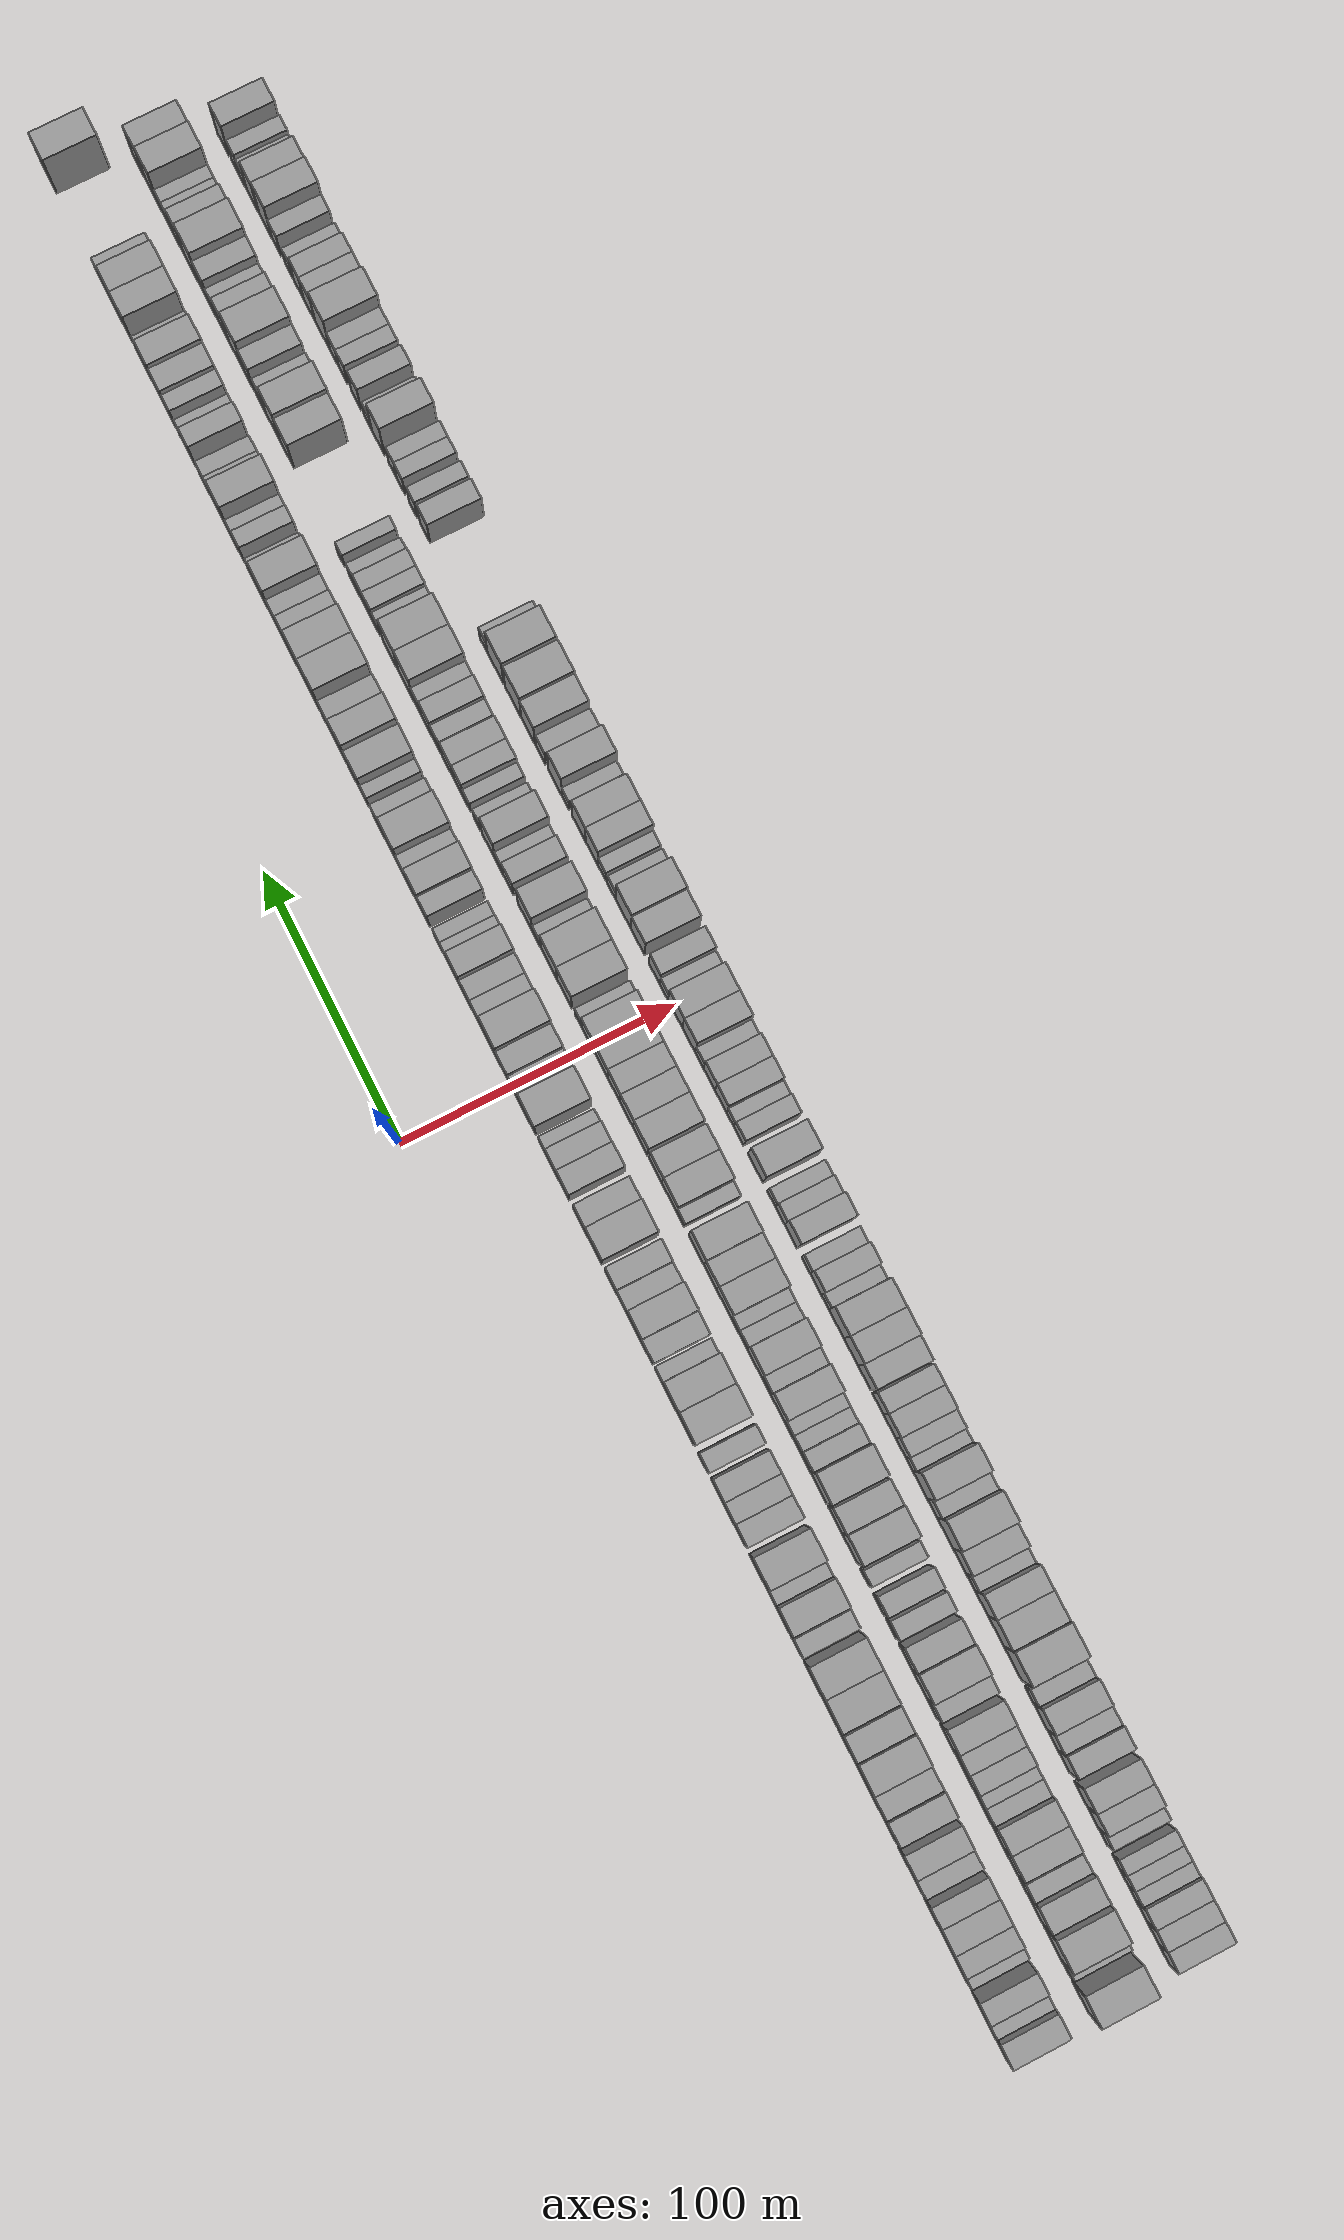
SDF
<sdf version="1.6">
 <world name="default">
  <scene>
   <sky><clouds><speed>12</speed></clouds></sky>
   <ambient>0.4 0.4 0.4 1</ambient>
   <background>0.7 0.7 0.7 1</background>
   <shadows>1</shadows>
  </scene>
  <gravity>0 0 -9.8066</gravity>
  <magnetic_field>6e-06 2.3e-05 -4.2e-05</magnetic_field>
  <physics default="0" name="default_physics" type="ode">
   <ode>
    <solver>
     <type>quick</type>
     <iters>10</iters>
     <sor>1.0</sor>
     <use_dynamic_moi_rescaling>0</use_dynamic_moi_rescaling>
    </solver>
    <constraints>
     <cfm>0</cfm>
     <erp>0.2</erp>
     <contact_max_correcting_vel>100</contact_max_correcting_vel>
     <contact_surface_layer>0.001</contact_surface_layer>
    </constraints>
   </ode>
   <max_step_size>0.004</max_step_size>
   <real_time_factor>1</real_time_factor>
   <real_time_update_rate>250</real_time_update_rate>
  </physics>
  <light name="sun" type="directional">
   <pose>0 0 10 0 0 0</pose>
   <diffuse>0.8 0.8 0.8 1</diffuse>
   <specular>0.2 0.2 0.2 1</specular>
   <attenuation>
    <range>1000</range>
    <constant>0.9</constant>
    <linear>0.01</linear>
    <quadratic>0.001</quadratic>
   </attenuation>
   <direction>-0.5 0.1 -0.9</direction>
  </light>
  <model name="building_1">
   <static>1</static>
   <pose>50.0000 -331.8723 0 0.000000 0.000000 0.000000</pose>
   <link name="link">
    <pose>0 0 9.00 0 0 0</pose>
    <collision name="collision"><geometry><box><size>20.0000 8.2555 18.0000</size></box></geometry></collision>
    <visual name="visual">
     <cast_shadows>0</cast_shadows>
     <geometry><box><size>20.0000 8.2555 18.0000</size></box></geometry>
     <material>
      <script>
       <uri>model://grey_wall/materials/scripts</uri>
       <uri>model://grey_wall/materials/textures</uri>
       <name>vrc/grey_wall</name>
      </script>
     </material>
    </visual>
   </link>
  </model>
  <model name="building_2">
   <static>1</static>
   <pose>50.0000 -324.7991 0 0.000000 0.000000 0.000000</pose>
   <link name="link">
    <pose>0 0 6.00 0 0 0</pose>
    <collision name="collision"><geometry><box><size>20.0000 5.8909 12.0000</size></box></geometry></collision>
    <visual name="visual">
     <cast_shadows>0</cast_shadows>
     <geometry><box><size>20.0000 5.8909 12.0000</size></box></geometry>
     <material>
      <script>
       <uri>model://grey_wall/materials/scripts</uri>
       <uri>model://grey_wall/materials/textures</uri>
       <name>vrc/grey_wall</name>
      </script>
     </material>
    </visual>
   </link>
  </model>
  <model name="building_3">
   <static>1</static>
   <pose>50.0000 -318.1477 0 0.000000 0.000000 0.000000</pose>
   <link name="link">
    <pose>0 0 9.00 0 0 0</pose>
    <collision name="collision"><geometry><box><size>20.0000 7.4118 18.0000</size></box></geometry></collision>
    <visual name="visual">
     <cast_shadows>0</cast_shadows>
     <geometry><box><size>20.0000 7.4118 18.0000</size></box></geometry>
     <material>
      <script>
       <uri>model://grey_wall/materials/scripts</uri>
       <uri>model://grey_wall/materials/textures</uri>
       <name>vrc/grey_wall</name>
      </script>
     </material>
    </visual>
   </link>
  </model>
  <model name="building_4">
   <static>1</static>
   <pose>50.0000 -308.9618 0 0.000000 0.000000 0.000000</pose>
   <link name="link">
    <pose>0 0 6.00 0 0 0</pose>
    <collision name="collision"><geometry><box><size>20.0000 4.9599 12.0000</size></box></geometry></collision>
    <visual name="visual">
     <cast_shadows>0</cast_shadows>
     <geometry><box><size>20.0000 4.9599 12.0000</size></box></geometry>
     <material>
      <script>
       <uri>model://grey_wall/materials/scripts</uri>
       <uri>model://grey_wall/materials/textures</uri>
       <name>vrc/grey_wall</name>
      </script>
     </material>
    </visual>
   </link>
  </model>
  <model name="building_5">
   <static>1</static>
   <pose>50.0000 -302.8142 0 0.000000 0.000000 0.000000</pose>
   <link name="link">
    <pose>0 0 9.00 0 0 0</pose>
    <collision name="collision"><geometry><box><size>20.0000 7.3353 18.0000</size></box></geometry></collision>
    <visual name="visual">
     <cast_shadows>0</cast_shadows>
     <geometry><box><size>20.0000 7.3353 18.0000</size></box></geometry>
     <material>
      <script>
       <uri>model://grey_wall/materials/scripts</uri>
       <uri>model://grey_wall/materials/textures</uri>
       <name>vrc/grey_wall</name>
      </script>
     </material>
    </visual>
   </link>
  </model>
  <model name="building_6">
   <static>1</static>
   <pose>50.0000 -294.8184 0 0.000000 0.000000 0.000000</pose>
   <link name="link">
    <pose>0 0 9.00 0 0 0</pose>
    <collision name="collision"><geometry><box><size>20.0000 8.6562 18.0000</size></box></geometry></collision>
    <visual name="visual">
     <cast_shadows>0</cast_shadows>
     <geometry><box><size>20.0000 8.6562 18.0000</size></box></geometry>
     <material>
      <script>
       <uri>model://grey_wall/materials/scripts</uri>
       <uri>model://grey_wall/materials/textures</uri>
       <name>vrc/grey_wall</name>
      </script>
     </material>
    </visual>
   </link>
  </model>
  <model name="building_7">
   <static>1</static>
   <pose>50.0000 -286.8759 0 0.000000 0.000000 0.000000</pose>
   <link name="link">
    <pose>0 0 9.00 0 0 0</pose>
    <collision name="collision"><geometry><box><size>20.0000 7.2289 18.0000</size></box></geometry></collision>
    <visual name="visual">
     <cast_shadows>0</cast_shadows>
     <geometry><box><size>20.0000 7.2289 18.0000</size></box></geometry>
     <material>
      <script>
       <uri>model://grey_wall/materials/scripts</uri>
       <uri>model://grey_wall/materials/textures</uri>
       <name>vrc/grey_wall</name>
      </script>
     </material>
    </visual>
   </link>
  </model>
  <model name="building_8">
   <static>1</static>
   <pose>50.0000 -277.8663 0 0.000000 0.000000 0.000000</pose>
   <link name="link">
    <pose>0 0 7.50 0 0 0</pose>
    <collision name="collision"><geometry><box><size>20.0000 6.7901 15.0000</size></box></geometry></collision>
    <visual name="visual">
     <cast_shadows>0</cast_shadows>
     <geometry><box><size>20.0000 6.7901 15.0000</size></box></geometry>
     <material>
      <script>
       <uri>model://grey_wall/materials/scripts</uri>
       <uri>model://grey_wall/materials/textures</uri>
       <name>vrc/grey_wall</name>
      </script>
     </material>
    </visual>
   </link>
  </model>
  <model name="building_9">
   <static>1</static>
   <pose>50.0000 -270.3307 0 0.000000 0.000000 0.000000</pose>
   <link name="link">
    <pose>0 0 9.00 0 0 0</pose>
    <collision name="collision"><geometry><box><size>20.0000 8.2811 18.0000</size></box></geometry></collision>
    <visual name="visual">
     <cast_shadows>0</cast_shadows>
     <geometry><box><size>20.0000 8.2811 18.0000</size></box></geometry>
     <material>
      <script>
       <uri>model://grey_wall/materials/scripts</uri>
       <uri>model://grey_wall/materials/textures</uri>
       <name>vrc/grey_wall</name>
      </script>
     </material>
    </visual>
   </link>
  </model>
  <model name="building_10">
   <static>1</static>
   <pose>50.0000 -258.9902 0 0.000000 0.000000 0.000000</pose>
   <link name="link">
    <pose>0 0 10.50 0 0 0</pose>
    <collision name="collision"><geometry><box><size>20.0000 8.4001 21.0000</size></box></geometry></collision>
    <visual name="visual">
     <cast_shadows>0</cast_shadows>
     <geometry><box><size>20.0000 8.4001 21.0000</size></box></geometry>
     <material>
      <script>
       <uri>model://grey_wall/materials/scripts</uri>
       <uri>model://grey_wall/materials/textures</uri>
       <name>vrc/grey_wall</name>
      </script>
     </material>
    </visual>
   </link>
  </model>
  <model name="building_11">
   <static>1</static>
   <pose>50.0000 -250.2972 0 0.000000 0.000000 0.000000</pose>
   <link name="link">
    <pose>0 0 9.00 0 0 0</pose>
    <collision name="collision"><geometry><box><size>20.0000 8.9858 18.0000</size></box></geometry></collision>
    <visual name="visual">
     <cast_shadows>0</cast_shadows>
     <geometry><box><size>20.0000 8.9858 18.0000</size></box></geometry>
     <material>
      <script>
       <uri>model://grey_wall/materials/scripts</uri>
       <uri>model://grey_wall/materials/textures</uri>
       <name>vrc/grey_wall</name>
      </script>
     </material>
    </visual>
   </link>
  </model>
  <model name="building_12">
   <static>1</static>
   <pose>50.0000 -240.5236 0 0.000000 0.000000 0.000000</pose>
   <link name="link">
    <pose>0 0 12.00 0 0 0</pose>
    <collision name="collision"><geometry><box><size>20.0000 10.5614 24.0000</size></box></geometry></collision>
    <visual name="visual">
     <cast_shadows>0</cast_shadows>
     <geometry><box><size>20.0000 10.5614 24.0000</size></box></geometry>
     <material>
      <script>
       <uri>model://grey_wall/materials/scripts</uri>
       <uri>model://grey_wall/materials/textures</uri>
       <name>vrc/grey_wall</name>
      </script>
     </material>
    </visual>
   </link>
  </model>
  <model name="building_13">
   <static>1</static>
   <pose>50.0000 -230.7263 0 0.000000 0.000000 0.000000</pose>
   <link name="link">
    <pose>0 0 10.50 0 0 0</pose>
    <collision name="collision"><geometry><box><size>20.0000 9.0333 21.0000</size></box></geometry></collision>
    <visual name="visual">
     <cast_shadows>0</cast_shadows>
     <geometry><box><size>20.0000 9.0333 21.0000</size></box></geometry>
     <material>
      <script>
       <uri>model://grey_wall/materials/scripts</uri>
       <uri>model://grey_wall/materials/textures</uri>
       <name>vrc/grey_wall</name>
      </script>
     </material>
    </visual>
   </link>
  </model>
  <model name="building_14">
   <static>1</static>
   <pose>50.0000 -219.5225 0 0.000000 0.000000 0.000000</pose>
   <link name="link">
    <pose>0 0 12.00 0 0 0</pose>
    <collision name="collision"><geometry><box><size>20.0000 11.3742 24.0000</size></box></geometry></collision>
    <visual name="visual">
     <cast_shadows>0</cast_shadows>
     <geometry><box><size>20.0000 11.3742 24.0000</size></box></geometry>
     <material>
      <script>
       <uri>model://grey_wall/materials/scripts</uri>
       <uri>model://grey_wall/materials/textures</uri>
       <name>vrc/grey_wall</name>
      </script>
     </material>
    </visual>
   </link>
  </model>
  <model name="building_15">
   <static>1</static>
   <pose>50.0000 -208.3464 0 0.000000 0.000000 0.000000</pose>
   <link name="link">
    <pose>0 0 12.00 0 0 0</pose>
    <collision name="collision"><geometry><box><size>20.0000 10.9780 24.0000</size></box></geometry></collision>
    <visual name="visual">
     <cast_shadows>0</cast_shadows>
     <geometry><box><size>20.0000 10.9780 24.0000</size></box></geometry>
     <material>
      <script>
       <uri>model://grey_wall/materials/scripts</uri>
       <uri>model://grey_wall/materials/textures</uri>
       <name>vrc/grey_wall</name>
      </script>
     </material>
    </visual>
   </link>
  </model>
  <model name="building_16">
   <static>1</static>
   <pose>50.0000 -197.5580 0 0.000000 0.000000 0.000000</pose>
   <link name="link">
    <pose>0 0 7.50 0 0 0</pose>
    <collision name="collision"><geometry><box><size>20.0000 6.5987 15.0000</size></box></geometry></collision>
    <visual name="visual">
     <cast_shadows>0</cast_shadows>
     <geometry><box><size>20.0000 6.5987 15.0000</size></box></geometry>
     <material>
      <script>
       <uri>model://grey_wall/materials/scripts</uri>
       <uri>model://grey_wall/materials/textures</uri>
       <name>vrc/grey_wall</name>
      </script>
     </material>
    </visual>
   </link>
  </model>
  <model name="building_17">
   <static>1</static>
   <pose>50.0000 -188.2668 0 0.000000 0.000000 0.000000</pose>
   <link name="link">
    <pose>0 0 10.50 0 0 0</pose>
    <collision name="collision"><geometry><box><size>20.0000 9.9837 21.0000</size></box></geometry></collision>
    <visual name="visual">
     <cast_shadows>0</cast_shadows>
     <geometry><box><size>20.0000 9.9837 21.0000</size></box></geometry>
     <material>
      <script>
       <uri>model://grey_wall/materials/scripts</uri>
       <uri>model://grey_wall/materials/textures</uri>
       <name>vrc/grey_wall</name>
      </script>
     </material>
    </visual>
   </link>
  </model>
  <model name="building_18">
   <static>1</static>
   <pose>50.0000 -180.3005 0 0.000000 0.000000 0.000000</pose>
   <link name="link">
    <pose>0 0 6.00 0 0 0</pose>
    <collision name="collision"><geometry><box><size>20.0000 5.9488 12.0000</size></box></geometry></collision>
    <visual name="visual">
     <cast_shadows>0</cast_shadows>
     <geometry><box><size>20.0000 5.9488 12.0000</size></box></geometry>
     <material>
      <script>
       <uri>model://grey_wall/materials/scripts</uri>
       <uri>model://grey_wall/materials/textures</uri>
       <name>vrc/grey_wall</name>
      </script>
     </material>
    </visual>
   </link>
  </model>
  <model name="building_19">
   <static>1</static>
   <pose>50.0000 -171.7092 0 0.000000 0.000000 0.000000</pose>
   <link name="link">
    <pose>0 0 12.00 0 0 0</pose>
    <collision name="collision"><geometry><box><size>20.0000 11.2336 24.0000</size></box></geometry></collision>
    <visual name="visual">
     <cast_shadows>0</cast_shadows>
     <geometry><box><size>20.0000 11.2336 24.0000</size></box></geometry>
     <material>
      <script>
       <uri>model://grey_wall/materials/scripts</uri>
       <uri>model://grey_wall/materials/textures</uri>
       <name>vrc/grey_wall</name>
      </script>
     </material>
    </visual>
   </link>
  </model>
  <model name="building_20">
   <static>1</static>
   <pose>50.0000 -159.1138 0 0.000000 0.000000 0.000000</pose>
   <link name="link">
    <pose>0 0 9.00 0 0 0</pose>
    <collision name="collision"><geometry><box><size>20.0000 7.9572 18.0000</size></box></geometry></collision>
    <visual name="visual">
     <cast_shadows>0</cast_shadows>
     <geometry><box><size>20.0000 7.9572 18.0000</size></box></geometry>
     <material>
      <script>
       <uri>model://grey_wall/materials/scripts</uri>
       <uri>model://grey_wall/materials/textures</uri>
       <name>vrc/grey_wall</name>
      </script>
     </material>
    </visual>
   </link>
  </model>
  <model name="building_21">
   <static>1</static>
   <pose>50.0000 -151.4212 0 0.000000 0.000000 0.000000</pose>
   <link name="link">
    <pose>0 0 9.00 0 0 0</pose>
    <collision name="collision"><geometry><box><size>20.0000 7.4280 18.0000</size></box></geometry></collision>
    <visual name="visual">
     <cast_shadows>0</cast_shadows>
     <geometry><box><size>20.0000 7.4280 18.0000</size></box></geometry>
     <material>
      <script>
       <uri>model://grey_wall/materials/scripts</uri>
       <uri>model://grey_wall/materials/textures</uri>
       <name>vrc/grey_wall</name>
      </script>
     </material>
    </visual>
   </link>
  </model>
  <model name="building_22">
   <static>1</static>
   <pose>50.0000 -143.6685 0 0.000000 0.000000 0.000000</pose>
   <link name="link">
    <pose>0 0 9.00 0 0 0</pose>
    <collision name="collision"><geometry><box><size>20.0000 8.0774 18.0000</size></box></geometry></collision>
    <visual name="visual">
     <cast_shadows>0</cast_shadows>
     <geometry><box><size>20.0000 8.0774 18.0000</size></box></geometry>
     <material>
      <script>
       <uri>model://grey_wall/materials/scripts</uri>
       <uri>model://grey_wall/materials/textures</uri>
       <name>vrc/grey_wall</name>
      </script>
     </material>
    </visual>
   </link>
  </model>
  <model name="building_23">
   <static>1</static>
   <pose>50.0000 -134.2291 0 0.000000 0.000000 0.000000</pose>
   <link name="link">
    <pose>0 0 7.50 0 0 0</pose>
    <collision name="collision"><geometry><box><size>20.0000 6.8014 15.0000</size></box></geometry></collision>
    <visual name="visual">
     <cast_shadows>0</cast_shadows>
     <geometry><box><size>20.0000 6.8014 15.0000</size></box></geometry>
     <material>
      <script>
       <uri>model://grey_wall/materials/scripts</uri>
       <uri>model://grey_wall/materials/textures</uri>
       <name>vrc/grey_wall</name>
      </script>
     </material>
    </visual>
   </link>
  </model>
  <model name="building_24">
   <static>1</static>
   <pose>50.0000 -122.2531 0 0.000000 0.000000 0.000000</pose>
   <link name="link">
    <pose>0 0 12.00 0 0 0</pose>
    <collision name="collision"><geometry><box><size>20.0000 11.1506 24.0000</size></box></geometry></collision>
    <visual name="visual">
     <cast_shadows>0</cast_shadows>
     <geometry><box><size>20.0000 11.1506 24.0000</size></box></geometry>
     <material>
      <script>
       <uri>model://grey_wall/materials/scripts</uri>
       <uri>model://grey_wall/materials/textures</uri>
       <name>vrc/grey_wall</name>
      </script>
     </material>
    </visual>
   </link>
  </model>
  <model name="building_25">
   <static>1</static>
   <pose>50.0000 -111.4234 0 0.000000 0.000000 0.000000</pose>
   <link name="link">
    <pose>0 0 12.00 0 0 0</pose>
    <collision name="collision"><geometry><box><size>20.0000 10.5088 24.0000</size></box></geometry></collision>
    <visual name="visual">
     <cast_shadows>0</cast_shadows>
     <geometry><box><size>20.0000 10.5088 24.0000</size></box></geometry>
     <material>
      <script>
       <uri>model://grey_wall/materials/scripts</uri>
       <uri>model://grey_wall/materials/textures</uri>
       <name>vrc/grey_wall</name>
      </script>
     </material>
    </visual>
   </link>
  </model>
  <model name="building_26">
   <static>1</static>
   <pose>50.0000 -103.4471 0 0.000000 0.000000 0.000000</pose>
   <link name="link">
    <pose>0 0 6.00 0 0 0</pose>
    <collision name="collision"><geometry><box><size>20.0000 5.4438 12.0000</size></box></geometry></collision>
    <visual name="visual">
     <cast_shadows>0</cast_shadows>
     <geometry><box><size>20.0000 5.4438 12.0000</size></box></geometry>
     <material>
      <script>
       <uri>model://grey_wall/materials/scripts</uri>
       <uri>model://grey_wall/materials/textures</uri>
       <name>vrc/grey_wall</name>
      </script>
     </material>
    </visual>
   </link>
  </model>
  <model name="building_27">
   <static>1</static>
   <pose>50.0000 -95.6076 0 0.000000 0.000000 0.000000</pose>
   <link name="link">
    <pose>0 0 9.00 0 0 0</pose>
    <collision name="collision"><geometry><box><size>20.0000 8.2350 18.0000</size></box></geometry></collision>
    <visual name="visual">
     <cast_shadows>0</cast_shadows>
     <geometry><box><size>20.0000 8.2350 18.0000</size></box></geometry>
     <material>
      <script>
       <uri>model://grey_wall/materials/scripts</uri>
       <uri>model://grey_wall/materials/textures</uri>
       <name>vrc/grey_wall</name>
      </script>
     </material>
    </visual>
   </link>
  </model>
  <model name="building_28">
   <static>1</static>
   <pose>50.0000 -86.5173 0 0.000000 0.000000 0.000000</pose>
   <link name="link">
    <pose>0 0 12.00 0 0 0</pose>
    <collision name="collision"><geometry><box><size>20.0000 9.9456 24.0000</size></box></geometry></collision>
    <visual name="visual">
     <cast_shadows>0</cast_shadows>
     <geometry><box><size>20.0000 9.9456 24.0000</size></box></geometry>
     <material>
      <script>
       <uri>model://grey_wall/materials/scripts</uri>
       <uri>model://grey_wall/materials/textures</uri>
       <name>vrc/grey_wall</name>
      </script>
     </material>
    </visual>
   </link>
  </model>
  <model name="building_29">
   <static>1</static>
   <pose>50.0000 -77.8846 0 0.000000 0.000000 0.000000</pose>
   <link name="link">
    <pose>0 0 7.50 0 0 0</pose>
    <collision name="collision"><geometry><box><size>20.0000 7.3198 15.0000</size></box></geometry></collision>
    <visual name="visual">
     <cast_shadows>0</cast_shadows>
     <geometry><box><size>20.0000 7.3198 15.0000</size></box></geometry>
     <material>
      <script>
       <uri>model://grey_wall/materials/scripts</uri>
       <uri>model://grey_wall/materials/textures</uri>
       <name>vrc/grey_wall</name>
      </script>
     </material>
    </visual>
   </link>
  </model>
  <model name="building_30">
   <static>1</static>
   <pose>50.0000 -70.1955 0 0.000000 0.000000 0.000000</pose>
   <link name="link">
    <pose>0 0 9.00 0 0 0</pose>
    <collision name="collision"><geometry><box><size>20.0000 8.0583 18.0000</size></box></geometry></collision>
    <visual name="visual">
     <cast_shadows>0</cast_shadows>
     <geometry><box><size>20.0000 8.0583 18.0000</size></box></geometry>
     <material>
      <script>
       <uri>model://grey_wall/materials/scripts</uri>
       <uri>model://grey_wall/materials/textures</uri>
       <name>vrc/grey_wall</name>
      </script>
     </material>
    </visual>
   </link>
  </model>
  <model name="building_31">
   <static>1</static>
   <pose>50.0000 -58.3696 0 0.000000 0.000000 0.000000</pose>
   <link name="link">
    <pose>0 0 12.00 0 0 0</pose>
    <collision name="collision"><geometry><box><size>20.0000 11.5935 24.0000</size></box></geometry></collision>
    <visual name="visual">
     <cast_shadows>0</cast_shadows>
     <geometry><box><size>20.0000 11.5935 24.0000</size></box></geometry>
     <material>
      <script>
       <uri>model://grey_wall/materials/scripts</uri>
       <uri>model://grey_wall/materials/textures</uri>
       <name>vrc/grey_wall</name>
      </script>
     </material>
    </visual>
   </link>
  </model>
  <model name="building_32">
   <static>1</static>
   <pose>50.0000 -48.3083 0 0.000000 0.000000 0.000000</pose>
   <link name="link">
    <pose>0 0 9.00 0 0 0</pose>
    <collision name="collision"><geometry><box><size>20.0000 8.5291 18.0000</size></box></geometry></collision>
    <visual name="visual">
     <cast_shadows>0</cast_shadows>
     <geometry><box><size>20.0000 8.5291 18.0000</size></box></geometry>
     <material>
      <script>
       <uri>model://grey_wall/materials/scripts</uri>
       <uri>model://grey_wall/materials/textures</uri>
       <name>vrc/grey_wall</name>
      </script>
     </material>
    </visual>
   </link>
  </model>
  <model name="building_33">
   <static>1</static>
   <pose>50.0000 -36.6462 0 0.000000 0.000000 0.000000</pose>
   <link name="link">
    <pose>0 0 10.50 0 0 0</pose>
    <collision name="collision"><geometry><box><size>20.0000 8.7952 21.0000</size></box></geometry></collision>
    <visual name="visual">
     <cast_shadows>0</cast_shadows>
     <geometry><box><size>20.0000 8.7952 21.0000</size></box></geometry>
     <material>
      <script>
       <uri>model://grey_wall/materials/scripts</uri>
       <uri>model://grey_wall/materials/textures</uri>
       <name>vrc/grey_wall</name>
      </script>
     </material>
    </visual>
   </link>
  </model>
  <model name="building_34">
   <static>1</static>
   <pose>50.0000 -28.3335 0 0.000000 0.000000 0.000000</pose>
   <link name="link">
    <pose>0 0 9.00 0 0 0</pose>
    <collision name="collision"><geometry><box><size>20.0000 7.8303 18.0000</size></box></geometry></collision>
    <visual name="visual">
     <cast_shadows>0</cast_shadows>
     <geometry><box><size>20.0000 7.8303 18.0000</size></box></geometry>
     <material>
      <script>
       <uri>model://grey_wall/materials/scripts</uri>
       <uri>model://grey_wall/materials/textures</uri>
       <name>vrc/grey_wall</name>
      </script>
     </material>
    </visual>
   </link>
  </model>
  <model name="building_35">
   <static>1</static>
   <pose>50.0000 -21.9060 0 0.000000 0.000000 0.000000</pose>
   <link name="link">
    <pose>0 0 6.00 0 0 0</pose>
    <collision name="collision"><geometry><box><size>20.0000 5.0245 12.0000</size></box></geometry></collision>
    <visual name="visual">
     <cast_shadows>0</cast_shadows>
     <geometry><box><size>20.0000 5.0245 12.0000</size></box></geometry>
     <material>
      <script>
       <uri>model://grey_wall/materials/scripts</uri>
       <uri>model://grey_wall/materials/textures</uri>
       <name>vrc/grey_wall</name>
      </script>
     </material>
    </visual>
   </link>
  </model>
  <model name="building_36">
   <static>1</static>
   <pose>50.0000 -11.4566 0 0.000000 0.000000 0.000000</pose>
   <link name="link">
    <pose>0 0 12.00 0 0 0</pose>
    <collision name="collision"><geometry><box><size>20.0000 11.8743 24.0000</size></box></geometry></collision>
    <visual name="visual">
     <cast_shadows>0</cast_shadows>
     <geometry><box><size>20.0000 11.8743 24.0000</size></box></geometry>
     <material>
      <script>
       <uri>model://grey_wall/materials/scripts</uri>
       <uri>model://grey_wall/materials/textures</uri>
       <name>vrc/grey_wall</name>
      </script>
     </material>
    </visual>
   </link>
  </model>
  <model name="building_37">
   <static>1</static>
   <pose>50.0000 -1.7803 0 0.000000 0.000000 0.000000</pose>
   <link name="link">
    <pose>0 0 7.50 0 0 0</pose>
    <collision name="collision"><geometry><box><size>20.0000 7.4783 15.0000</size></box></geometry></collision>
    <visual name="visual">
     <cast_shadows>0</cast_shadows>
     <geometry><box><size>20.0000 7.4783 15.0000</size></box></geometry>
     <material>
      <script>
       <uri>model://grey_wall/materials/scripts</uri>
       <uri>model://grey_wall/materials/textures</uri>
       <name>vrc/grey_wall</name>
      </script>
     </material>
    </visual>
   </link>
  </model>
  <model name="building_38">
   <static>1</static>
   <pose>50.0000 6.1895 0 0.000000 0.000000 0.000000</pose>
   <link name="link">
    <pose>0 0 9.00 0 0 0</pose>
    <collision name="collision"><geometry><box><size>20.0000 8.4613 18.0000</size></box></geometry></collision>
    <visual name="visual">
     <cast_shadows>0</cast_shadows>
     <geometry><box><size>20.0000 8.4613 18.0000</size></box></geometry>
     <material>
      <script>
       <uri>model://grey_wall/materials/scripts</uri>
       <uri>model://grey_wall/materials/textures</uri>
       <name>vrc/grey_wall</name>
      </script>
     </material>
    </visual>
   </link>
  </model>
  <model name="building_39">
   <static>1</static>
   <pose>50.0000 16.2375 0 0.000000 0.000000 0.000000</pose>
   <link name="link">
    <pose>0 0 12.00 0 0 0</pose>
    <collision name="collision"><geometry><box><size>20.0000 11.6348 24.0000</size></box></geometry></collision>
    <visual name="visual">
     <cast_shadows>0</cast_shadows>
     <geometry><box><size>20.0000 11.6348 24.0000</size></box></geometry>
     <material>
      <script>
       <uri>model://grey_wall/materials/scripts</uri>
       <uri>model://grey_wall/materials/textures</uri>
       <name>vrc/grey_wall</name>
      </script>
     </material>
    </visual>
   </link>
  </model>
  <model name="building_40">
   <static>1</static>
   <pose>50.0000 25.6012 0 0.000000 0.000000 0.000000</pose>
   <link name="link">
    <pose>0 0 7.50 0 0 0</pose>
    <collision name="collision"><geometry><box><size>20.0000 7.0926 15.0000</size></box></geometry></collision>
    <visual name="visual">
     <cast_shadows>0</cast_shadows>
     <geometry><box><size>20.0000 7.0926 15.0000</size></box></geometry>
     <material>
      <script>
       <uri>model://grey_wall/materials/scripts</uri>
       <uri>model://grey_wall/materials/textures</uri>
       <name>vrc/grey_wall</name>
      </script>
     </material>
    </visual>
   </link>
  </model>
  <model name="building_41">
   <static>1</static>
   <pose>50.0000 32.8756 0 0.000000 0.000000 0.000000</pose>
   <link name="link">
    <pose>0 0 7.50 0 0 0</pose>
    <collision name="collision"><geometry><box><size>20.0000 7.4560 15.0000</size></box></geometry></collision>
    <visual name="visual">
     <cast_shadows>0</cast_shadows>
     <geometry><box><size>20.0000 7.4560 15.0000</size></box></geometry>
     <material>
      <script>
       <uri>model://grey_wall/materials/scripts</uri>
       <uri>model://grey_wall/materials/textures</uri>
       <name>vrc/grey_wall</name>
      </script>
     </material>
    </visual>
   </link>
  </model>
  <model name="building_42">
   <static>1</static>
   <pose>50.0000 41.1588 0 0.000000 0.000000 0.000000</pose>
   <link name="link">
    <pose>0 0 10.50 0 0 0</pose>
    <collision name="collision"><geometry><box><size>20.0000 9.1105 21.0000</size></box></geometry></collision>
    <visual name="visual">
     <cast_shadows>0</cast_shadows>
     <geometry><box><size>20.0000 9.1105 21.0000</size></box></geometry>
     <material>
      <script>
       <uri>model://grey_wall/materials/scripts</uri>
       <uri>model://grey_wall/materials/textures</uri>
       <name>vrc/grey_wall</name>
      </script>
     </material>
    </visual>
   </link>
  </model>
  <model name="building_43">
   <static>1</static>
   <pose>50.0000 48.3113 0 0.000000 0.000000 0.000000</pose>
   <link name="link">
    <pose>0 0 6.00 0 0 0</pose>
    <collision name="collision"><geometry><box><size>20.0000 5.1945 12.0000</size></box></geometry></collision>
    <visual name="visual">
     <cast_shadows>0</cast_shadows>
     <geometry><box><size>20.0000 5.1945 12.0000</size></box></geometry>
     <material>
      <script>
       <uri>model://grey_wall/materials/scripts</uri>
       <uri>model://grey_wall/materials/textures</uri>
       <name>vrc/grey_wall</name>
      </script>
     </material>
    </visual>
   </link>
  </model>
  <model name="building_44">
   <static>1</static>
   <pose>50.0000 53.4789 0 0.000000 0.000000 0.000000</pose>
   <link name="link">
    <pose>0 0 6.00 0 0 0</pose>
    <collision name="collision"><geometry><box><size>20.0000 5.1407 12.0000</size></box></geometry></collision>
    <visual name="visual">
     <cast_shadows>0</cast_shadows>
     <geometry><box><size>20.0000 5.1407 12.0000</size></box></geometry>
     <material>
      <script>
       <uri>model://grey_wall/materials/scripts</uri>
       <uri>model://grey_wall/materials/textures</uri>
       <name>vrc/grey_wall</name>
      </script>
     </material>
    </visual>
   </link>
  </model>
  <model name="building_45">
   <static>1</static>
   <pose>50.0000 62.6525 0 0.000000 0.000000 0.000000</pose>
   <link name="link">
    <pose>0 0 9.00 0 0 0</pose>
    <collision name="collision"><geometry><box><size>20.0000 7.2066 18.0000</size></box></geometry></collision>
    <visual name="visual">
     <cast_shadows>0</cast_shadows>
     <geometry><box><size>20.0000 7.2066 18.0000</size></box></geometry>
     <material>
      <script>
       <uri>model://grey_wall/materials/scripts</uri>
       <uri>model://grey_wall/materials/textures</uri>
       <name>vrc/grey_wall</name>
      </script>
     </material>
    </visual>
   </link>
  </model>
  <model name="building_46">
   <static>1</static>
   <pose>50.0000 71.0401 0 0.000000 0.000000 0.000000</pose>
   <link name="link">
    <pose>0 0 10.50 0 0 0</pose>
    <collision name="collision"><geometry><box><size>20.0000 9.5687 21.0000</size></box></geometry></collision>
    <visual name="visual">
     <cast_shadows>0</cast_shadows>
     <geometry><box><size>20.0000 9.5687 21.0000</size></box></geometry>
     <material>
      <script>
       <uri>model://grey_wall/materials/scripts</uri>
       <uri>model://grey_wall/materials/textures</uri>
       <name>vrc/grey_wall</name>
      </script>
     </material>
    </visual>
   </link>
  </model>
  <model name="building_47">
   <static>1</static>
   <pose>50.0000 78.9659 0 0.000000 0.000000 0.000000</pose>
   <link name="link">
    <pose>0 0 7.50 0 0 0</pose>
    <collision name="collision"><geometry><box><size>20.0000 6.2827 15.0000</size></box></geometry></collision>
    <visual name="visual">
     <cast_shadows>0</cast_shadows>
     <geometry><box><size>20.0000 6.2827 15.0000</size></box></geometry>
     <material>
      <script>
       <uri>model://grey_wall/materials/scripts</uri>
       <uri>model://grey_wall/materials/textures</uri>
       <name>vrc/grey_wall</name>
      </script>
     </material>
    </visual>
   </link>
  </model>
  <model name="building_48">
   <static>1</static>
   <pose>50.0000 87.9736 0 0.000000 0.000000 0.000000</pose>
   <link name="link">
    <pose>0 0 12.00 0 0 0</pose>
    <collision name="collision"><geometry><box><size>20.0000 11.7327 24.0000</size></box></geometry></collision>
    <visual name="visual">
     <cast_shadows>0</cast_shadows>
     <geometry><box><size>20.0000 11.7327 24.0000</size></box></geometry>
     <material>
      <script>
       <uri>model://grey_wall/materials/scripts</uri>
       <uri>model://grey_wall/materials/textures</uri>
       <name>vrc/grey_wall</name>
      </script>
     </material>
    </visual>
   </link>
  </model>
  <model name="building_49">
   <static>1</static>
   <pose>50.0000 97.3768 0 0.000000 0.000000 0.000000</pose>
   <link name="link">
    <pose>0 0 7.50 0 0 0</pose>
    <collision name="collision"><geometry><box><size>20.0000 7.0737 15.0000</size></box></geometry></collision>
    <visual name="visual">
     <cast_shadows>0</cast_shadows>
     <geometry><box><size>20.0000 7.0737 15.0000</size></box></geometry>
     <material>
      <script>
       <uri>model://grey_wall/materials/scripts</uri>
       <uri>model://grey_wall/materials/textures</uri>
       <name>vrc/grey_wall</name>
      </script>
     </material>
    </visual>
   </link>
  </model>
  <model name="building_50">
   <static>1</static>
   <pose>50.0000 106.3409 0 0.000000 0.000000 0.000000</pose>
   <link name="link">
    <pose>0 0 6.00 0 0 0</pose>
    <collision name="collision"><geometry><box><size>20.0000 4.8545 12.0000</size></box></geometry></collision>
    <visual name="visual">
     <cast_shadows>0</cast_shadows>
     <geometry><box><size>20.0000 4.8545 12.0000</size></box></geometry>
     <material>
      <script>
       <uri>model://grey_wall/materials/scripts</uri>
       <uri>model://grey_wall/materials/textures</uri>
       <name>vrc/grey_wall</name>
      </script>
     </material>
    </visual>
   </link>
  </model>
  <model name="building_51">
   <static>1</static>
   <pose>50.0000 113.9751 0 0.000000 0.000000 0.000000</pose>
   <link name="link">
    <pose>0 0 10.50 0 0 0</pose>
    <collision name="collision"><geometry><box><size>20.0000 10.4141 21.0000</size></box></geometry></collision>
    <visual name="visual">
     <cast_shadows>0</cast_shadows>
     <geometry><box><size>20.0000 10.4141 21.0000</size></box></geometry>
     <material>
      <script>
       <uri>model://grey_wall/materials/scripts</uri>
       <uri>model://grey_wall/materials/textures</uri>
       <name>vrc/grey_wall</name>
      </script>
     </material>
    </visual>
   </link>
  </model>
  <model name="building_52">
   <static>1</static>
   <pose>50.0000 125.0453 0 0.000000 0.000000 0.000000</pose>
   <link name="link">
    <pose>0 0 12.00 0 0 0</pose>
    <collision name="collision"><geometry><box><size>20.0000 9.7262 24.0000</size></box></geometry></collision>
    <visual name="visual">
     <cast_shadows>0</cast_shadows>
     <geometry><box><size>20.0000 9.7262 24.0000</size></box></geometry>
     <material>
      <script>
       <uri>model://grey_wall/materials/scripts</uri>
       <uri>model://grey_wall/materials/textures</uri>
       <name>vrc/grey_wall</name>
      </script>
     </material>
    </visual>
   </link>
  </model>
  <model name="building_53">
   <static>1</static>
   <pose>50.0000 134.2618 0 0.000000 0.000000 0.000000</pose>
   <link name="link">
    <pose>0 0 9.00 0 0 0</pose>
    <collision name="collision"><geometry><box><size>20.0000 8.7068 18.0000</size></box></geometry></collision>
    <visual name="visual">
     <cast_shadows>0</cast_shadows>
     <geometry><box><size>20.0000 8.7068 18.0000</size></box></geometry>
     <material>
      <script>
       <uri>model://grey_wall/materials/scripts</uri>
       <uri>model://grey_wall/materials/textures</uri>
       <name>vrc/grey_wall</name>
      </script>
     </material>
    </visual>
   </link>
  </model>
  <model name="building_54">
   <static>1</static>
   <pose>50.0000 146.4818 0 0.000000 0.000000 0.000000</pose>
   <link name="link">
    <pose>0 0 12.00 0 0 0</pose>
    <collision name="collision"><geometry><box><size>20.0000 11.7331 24.0000</size></box></geometry></collision>
    <visual name="visual">
     <cast_shadows>0</cast_shadows>
     <geometry><box><size>20.0000 11.7331 24.0000</size></box></geometry>
     <material>
      <script>
       <uri>model://grey_wall/materials/scripts</uri>
       <uri>model://grey_wall/materials/textures</uri>
       <name>vrc/grey_wall</name>
      </script>
     </material>
    </visual>
   </link>
  </model>
  <model name="building_55">
   <static>1</static>
   <pose>50.0000 157.6588 0 0.000000 0.000000 0.000000</pose>
   <link name="link">
    <pose>0 0 12.00 0 0 0</pose>
    <collision name="collision"><geometry><box><size>20.0000 10.6210 24.0000</size></box></geometry></collision>
    <visual name="visual">
     <cast_shadows>0</cast_shadows>
     <geometry><box><size>20.0000 10.6210 24.0000</size></box></geometry>
     <material>
      <script>
       <uri>model://grey_wall/materials/scripts</uri>
       <uri>model://grey_wall/materials/textures</uri>
       <name>vrc/grey_wall</name>
      </script>
     </material>
    </visual>
   </link>
  </model>
  <model name="building_56">
   <static>1</static>
   <pose>50.0000 166.6477 0 0.000000 0.000000 0.000000</pose>
   <link name="link">
    <pose>0 0 9.00 0 0 0</pose>
    <collision name="collision"><geometry><box><size>20.0000 7.3567 18.0000</size></box></geometry></collision>
    <visual name="visual">
     <cast_shadows>0</cast_shadows>
     <geometry><box><size>20.0000 7.3567 18.0000</size></box></geometry>
     <material>
      <script>
       <uri>model://grey_wall/materials/scripts</uri>
       <uri>model://grey_wall/materials/textures</uri>
       <name>vrc/grey_wall</name>
      </script>
     </material>
    </visual>
   </link>
  </model>
  <model name="building_57">
   <static>1</static>
   <pose>50.0000 173.9100 0 0.000000 0.000000 0.000000</pose>
   <link name="link">
    <pose>0 0 7.50 0 0 0</pose>
    <collision name="collision"><geometry><box><size>20.0000 7.1679 15.0000</size></box></geometry></collision>
    <visual name="visual">
     <cast_shadows>0</cast_shadows>
     <geometry><box><size>20.0000 7.1679 15.0000</size></box></geometry>
     <material>
      <script>
       <uri>model://grey_wall/materials/scripts</uri>
       <uri>model://grey_wall/materials/textures</uri>
       <name>vrc/grey_wall</name>
      </script>
     </material>
    </visual>
   </link>
  </model>
  <model name="building_58">
   <static>1</static>
   <pose>50.0000 183.1012 0 0.000000 0.000000 0.000000</pose>
   <link name="link">
    <pose>0 0 12.00 0 0 0</pose>
    <collision name="collision"><geometry><box><size>20.0000 11.2146 24.0000</size></box></geometry></collision>
    <visual name="visual">
     <cast_shadows>0</cast_shadows>
     <geometry><box><size>20.0000 11.2146 24.0000</size></box></geometry>
     <material>
      <script>
       <uri>model://grey_wall/materials/scripts</uri>
       <uri>model://grey_wall/materials/textures</uri>
       <name>vrc/grey_wall</name>
      </script>
     </material>
    </visual>
   </link>
  </model>
  <model name="building_59">
   <static>1</static>
   <pose>50.0000 191.4912 0 0.000000 0.000000 0.000000</pose>
   <link name="link">
    <pose>0 0 6.00 0 0 0</pose>
    <collision name="collision"><geometry><box><size>20.0000 5.5652 12.0000</size></box></geometry></collision>
    <visual name="visual">
     <cast_shadows>0</cast_shadows>
     <geometry><box><size>20.0000 5.5652 12.0000</size></box></geometry>
     <material>
      <script>
       <uri>model://grey_wall/materials/scripts</uri>
       <uri>model://grey_wall/materials/textures</uri>
       <name>vrc/grey_wall</name>
      </script>
     </material>
    </visual>
   </link>
  </model>
  <model name="building_60">
   <static>1</static>
   <pose>50.0000 200.4604 0 0.000000 0.000000 0.000000</pose>
   <link name="link">
    <pose>0 0 7.50 0 0 0</pose>
    <collision name="collision"><geometry><box><size>20.0000 6.3732 15.0000</size></box></geometry></collision>
    <visual name="visual">
     <cast_shadows>0</cast_shadows>
     <geometry><box><size>20.0000 6.3732 15.0000</size></box></geometry>
     <material>
      <script>
       <uri>model://grey_wall/materials/scripts</uri>
       <uri>model://grey_wall/materials/textures</uri>
       <name>vrc/grey_wall</name>
      </script>
     </material>
    </visual>
   </link>
  </model>
  <model name="building_61">
   <static>1</static>
   <pose>50.0000 206.3600 0 0.000000 0.000000 0.000000</pose>
   <link name="link">
    <pose>0 0 6.00 0 0 0</pose>
    <collision name="collision"><geometry><box><size>20.0000 5.4259 12.0000</size></box></geometry></collision>
    <visual name="visual">
     <cast_shadows>0</cast_shadows>
     <geometry><box><size>20.0000 5.4259 12.0000</size></box></geometry>
     <material>
      <script>
       <uri>model://grey_wall/materials/scripts</uri>
       <uri>model://grey_wall/materials/textures</uri>
       <name>vrc/grey_wall</name>
      </script>
     </material>
    </visual>
   </link>
  </model>
  <model name="building_62">
   <static>1</static>
   <pose>50.0000 214.2156 0 0.000000 0.000000 0.000000</pose>
   <link name="link">
    <pose>0 0 12.00 0 0 0</pose>
    <collision name="collision"><geometry><box><size>20.0000 10.2854 24.0000</size></box></geometry></collision>
    <visual name="visual">
     <cast_shadows>0</cast_shadows>
     <geometry><box><size>20.0000 10.2854 24.0000</size></box></geometry>
     <material>
      <script>
       <uri>model://grey_wall/materials/scripts</uri>
       <uri>model://grey_wall/materials/textures</uri>
       <name>vrc/grey_wall</name>
      </script>
     </material>
    </visual>
   </link>
  </model>
  <model name="building_63">
   <static>1</static>
   <pose>50.0000 222.9986 0 0.000000 0.000000 0.000000</pose>
   <link name="link">
    <pose>0 0 6.00 0 0 0</pose>
    <collision name="collision"><geometry><box><size>20.0000 5.2804 12.0000</size></box></geometry></collision>
    <visual name="visual">
     <cast_shadows>0</cast_shadows>
     <geometry><box><size>20.0000 5.2804 12.0000</size></box></geometry>
     <material>
      <script>
       <uri>model://grey_wall/materials/scripts</uri>
       <uri>model://grey_wall/materials/textures</uri>
       <name>vrc/grey_wall</name>
      </script>
     </material>
    </visual>
   </link>
  </model>
  <model name="building_64">
   <static>1</static>
   <pose>50.0000 228.6378 0 0.000000 0.000000 0.000000</pose>
   <link name="link">
    <pose>0 0 6.00 0 0 0</pose>
    <collision name="collision"><geometry><box><size>20.0000 5.9982 12.0000</size></box></geometry></collision>
    <visual name="visual">
     <cast_shadows>0</cast_shadows>
     <geometry><box><size>20.0000 5.9982 12.0000</size></box></geometry>
     <material>
      <script>
       <uri>model://grey_wall/materials/scripts</uri>
       <uri>model://grey_wall/materials/textures</uri>
       <name>vrc/grey_wall</name>
      </script>
     </material>
    </visual>
   </link>
  </model>
  <model name="building_65">
   <static>1</static>
   <pose>50.0000 238.3654 0 0.000000 0.000000 0.000000</pose>
   <link name="link">
    <pose>0 0 9.00 0 0 0</pose>
    <collision name="collision"><geometry><box><size>20.0000 7.4569 18.0000</size></box></geometry></collision>
    <visual name="visual">
     <cast_shadows>0</cast_shadows>
     <geometry><box><size>20.0000 7.4569 18.0000</size></box></geometry>
     <material>
      <script>
       <uri>model://grey_wall/materials/scripts</uri>
       <uri>model://grey_wall/materials/textures</uri>
       <name>vrc/grey_wall</name>
      </script>
     </material>
    </visual>
   </link>
  </model>
  <model name="building_66">
   <static>1</static>
   <pose>50.0000 244.9169 0 0.000000 0.000000 0.000000</pose>
   <link name="link">
    <pose>0 0 6.00 0 0 0</pose>
    <collision name="collision"><geometry><box><size>20.0000 5.6462 12.0000</size></box></geometry></collision>
    <visual name="visual">
     <cast_shadows>0</cast_shadows>
     <geometry><box><size>20.0000 5.6462 12.0000</size></box></geometry>
     <material>
      <script>
       <uri>model://grey_wall/materials/scripts</uri>
       <uri>model://grey_wall/materials/textures</uri>
       <name>vrc/grey_wall</name>
      </script>
     </material>
    </visual>
   </link>
  </model>
  <model name="building_67">
   <static>1</static>
   <pose>50.0000 252.8970 0 0.000000 0.000000 0.000000</pose>
   <link name="link">
    <pose>0 0 7.50 0 0 0</pose>
    <collision name="collision"><geometry><box><size>20.0000 6.3140 15.0000</size></box></geometry></collision>
    <visual name="visual">
     <cast_shadows>0</cast_shadows>
     <geometry><box><size>20.0000 6.3140 15.0000</size></box></geometry>
     <material>
      <script>
       <uri>model://grey_wall/materials/scripts</uri>
       <uri>model://grey_wall/materials/textures</uri>
       <name>vrc/grey_wall</name>
      </script>
     </material>
    </visual>
   </link>
  </model>
  <model name="building_68">
   <static>1</static>
   <pose>50.0000 260.4261 0 0.000000 0.000000 0.000000</pose>
   <link name="link">
    <pose>0 0 9.00 0 0 0</pose>
    <collision name="collision"><geometry><box><size>20.0000 8.7442 18.0000</size></box></geometry></collision>
    <visual name="visual">
     <cast_shadows>0</cast_shadows>
     <geometry><box><size>20.0000 8.7442 18.0000</size></box></geometry>
     <material>
      <script>
       <uri>model://grey_wall/materials/scripts</uri>
       <uri>model://grey_wall/materials/textures</uri>
       <name>vrc/grey_wall</name>
      </script>
     </material>
    </visual>
   </link>
  </model>
  <model name="building_69">
   <static>1</static>
   <pose>50.0000 269.7042 0 0.000000 0.000000 0.000000</pose>
   <link name="link">
    <pose>0 0 10.50 0 0 0</pose>
    <collision name="collision"><geometry><box><size>20.0000 9.8119 21.0000</size></box></geometry></collision>
    <visual name="visual">
     <cast_shadows>0</cast_shadows>
     <geometry><box><size>20.0000 9.8119 21.0000</size></box></geometry>
     <material>
      <script>
       <uri>model://grey_wall/materials/scripts</uri>
       <uri>model://grey_wall/materials/textures</uri>
       <name>vrc/grey_wall</name>
      </script>
     </material>
    </visual>
   </link>
  </model>
  <model name="building_70">
   <static>1</static>
   <pose>50.0000 277.4177 0 0.000000 0.000000 0.000000</pose>
   <link name="link">
    <pose>0 0 6.00 0 0 0</pose>
    <collision name="collision"><geometry><box><size>20.0000 5.6151 12.0000</size></box></geometry></collision>
    <visual name="visual">
     <cast_shadows>0</cast_shadows>
     <geometry><box><size>20.0000 5.6151 12.0000</size></box></geometry>
     <material>
      <script>
       <uri>model://grey_wall/materials/scripts</uri>
       <uri>model://grey_wall/materials/textures</uri>
       <name>vrc/grey_wall</name>
      </script>
     </material>
    </visual>
   </link>
  </model>
  <model name="building_71">
   <static>1</static>
   <pose>50.0000 288.2781 0 0.000000 0.000000 0.000000</pose>
   <link name="link">
    <pose>0 0 10.50 0 0 0</pose>
    <collision name="collision"><geometry><box><size>20.0000 10.1058 21.0000</size></box></geometry></collision>
    <visual name="visual">
     <cast_shadows>0</cast_shadows>
     <geometry><box><size>20.0000 10.1058 21.0000</size></box></geometry>
     <material>
      <script>
       <uri>model://grey_wall/materials/scripts</uri>
       <uri>model://grey_wall/materials/textures</uri>
       <name>vrc/grey_wall</name>
      </script>
     </material>
    </visual>
   </link>
  </model>
  <model name="building_72">
   <static>1</static>
   <pose>50.0000 298.3959 0 0.000000 0.000000 0.000000</pose>
   <link name="link">
    <pose>0 0 10.50 0 0 0</pose>
    <collision name="collision"><geometry><box><size>20.0000 10.1297 21.0000</size></box></geometry></collision>
    <visual name="visual">
     <cast_shadows>0</cast_shadows>
     <geometry><box><size>20.0000 10.1297 21.0000</size></box></geometry>
     <material>
      <script>
       <uri>model://grey_wall/materials/scripts</uri>
       <uri>model://grey_wall/materials/textures</uri>
       <name>vrc/grey_wall</name>
      </script>
     </material>
    </visual>
   </link>
  </model>
  <model name="building_73">
   <static>1</static>
   <pose>50.0000 308.2839 0 0.000000 0.000000 0.000000</pose>
   <link name="link">
    <pose>0 0 6.00 0 0 0</pose>
    <collision name="collision"><geometry><box><size>20.0000 5.6463 12.0000</size></box></geometry></collision>
    <visual name="visual">
     <cast_shadows>0</cast_shadows>
     <geometry><box><size>20.0000 5.6463 12.0000</size></box></geometry>
     <material>
      <script>
       <uri>model://grey_wall/materials/scripts</uri>
       <uri>model://grey_wall/materials/textures</uri>
       <name>vrc/grey_wall</name>
      </script>
     </material>
    </visual>
   </link>
  </model>
  <model name="building_74">
   <static>1</static>
   <pose>50.0000 348.5858 0 0.000000 0.000000 0.000000</pose>
   <link name="link">
    <pose>0 0 12.00 0 0 0</pose>
    <collision name="collision"><geometry><box><size>20.0000 10.9858 24.0000</size></box></geometry></collision>
    <visual name="visual">
     <cast_shadows>0</cast_shadows>
     <geometry><box><size>20.0000 10.9858 24.0000</size></box></geometry>
     <material>
      <script>
       <uri>model://grey_wall/materials/scripts</uri>
       <uri>model://grey_wall/materials/textures</uri>
       <name>vrc/grey_wall</name>
      </script>
     </material>
    </visual>
   </link>
  </model>
  <model name="building_75">
   <static>1</static>
   <pose>79.0000 -330.7034 0 0.000000 0.000000 0.000000</pose>
   <link name="link">
    <pose>0 0 12.00 0 0 0</pose>
    <collision name="collision"><geometry><box><size>20.0000 10.5932 24.0000</size></box></geometry></collision>
    <visual name="visual">
     <cast_shadows>0</cast_shadows>
     <geometry><box><size>20.0000 10.5932 24.0000</size></box></geometry>
     <material>
      <script>
       <uri>model://grey_wall/materials/scripts</uri>
       <uri>model://grey_wall/materials/textures</uri>
       <name>vrc/grey_wall</name>
      </script>
     </material>
    </visual>
   </link>
  </model>
  <model name="building_76">
   <static>1</static>
   <pose>79.0000 -320.9706 0 0.000000 0.000000 0.000000</pose>
   <link name="link">
    <pose>0 0 6.00 0 0 0</pose>
    <collision name="collision"><geometry><box><size>20.0000 4.8725 12.0000</size></box></geometry></collision>
    <visual name="visual">
     <cast_shadows>0</cast_shadows>
     <geometry><box><size>20.0000 4.8725 12.0000</size></box></geometry>
     <material>
      <script>
       <uri>model://grey_wall/materials/scripts</uri>
       <uri>model://grey_wall/materials/textures</uri>
       <name>vrc/grey_wall</name>
      </script>
     </material>
    </visual>
   </link>
  </model>
  <model name="building_77">
   <static>1</static>
   <pose>79.0000 -312.9926 0 0.000000 0.000000 0.000000</pose>
   <link name="link">
    <pose>0 0 12.00 0 0 0</pose>
    <collision name="collision"><geometry><box><size>20.0000 11.0833 24.0000</size></box></geometry></collision>
    <visual name="visual">
     <cast_shadows>0</cast_shadows>
     <geometry><box><size>20.0000 11.0833 24.0000</size></box></geometry>
     <material>
      <script>
       <uri>model://grey_wall/materials/scripts</uri>
       <uri>model://grey_wall/materials/textures</uri>
       <name>vrc/grey_wall</name>
      </script>
     </material>
    </visual>
   </link>
  </model>
  <model name="building_78">
   <static>1</static>
   <pose>79.0000 -301.8425 0 0.000000 0.000000 0.000000</pose>
   <link name="link">
    <pose>0 0 10.50 0 0 0</pose>
    <collision name="collision"><geometry><box><size>20.0000 9.2170 21.0000</size></box></geometry></collision>
    <visual name="visual">
     <cast_shadows>0</cast_shadows>
     <geometry><box><size>20.0000 9.2170 21.0000</size></box></geometry>
     <material>
      <script>
       <uri>model://grey_wall/materials/scripts</uri>
       <uri>model://grey_wall/materials/textures</uri>
       <name>vrc/grey_wall</name>
      </script>
     </material>
    </visual>
   </link>
  </model>
  <model name="building_79">
   <static>1</static>
   <pose>79.0000 -294.0895 0 0.000000 0.000000 0.000000</pose>
   <link name="link">
    <pose>0 0 7.50 0 0 0</pose>
    <collision name="collision"><geometry><box><size>20.0000 6.2889 15.0000</size></box></geometry></collision>
    <visual name="visual">
     <cast_shadows>0</cast_shadows>
     <geometry><box><size>20.0000 6.2889 15.0000</size></box></geometry>
     <material>
      <script>
       <uri>model://grey_wall/materials/scripts</uri>
       <uri>model://grey_wall/materials/textures</uri>
       <name>vrc/grey_wall</name>
      </script>
     </material>
    </visual>
   </link>
  </model>
  <model name="building_80">
   <static>1</static>
   <pose>79.0000 -285.5408 0 0.000000 0.000000 0.000000</pose>
   <link name="link">
    <pose>0 0 9.00 0 0 0</pose>
    <collision name="collision"><geometry><box><size>20.0000 8.8086 18.0000</size></box></geometry></collision>
    <visual name="visual">
     <cast_shadows>0</cast_shadows>
     <geometry><box><size>20.0000 8.8086 18.0000</size></box></geometry>
     <material>
      <script>
       <uri>model://grey_wall/materials/scripts</uri>
       <uri>model://grey_wall/materials/textures</uri>
       <name>vrc/grey_wall</name>
      </script>
     </material>
    </visual>
   </link>
  </model>
  <model name="building_81">
   <static>1</static>
   <pose>79.0000 -276.7729 0 0.000000 0.000000 0.000000</pose>
   <link name="link">
    <pose>0 0 9.00 0 0 0</pose>
    <collision name="collision"><geometry><box><size>20.0000 8.7271 18.0000</size></box></geometry></collision>
    <visual name="visual">
     <cast_shadows>0</cast_shadows>
     <geometry><box><size>20.0000 8.7271 18.0000</size></box></geometry>
     <material>
      <script>
       <uri>model://grey_wall/materials/scripts</uri>
       <uri>model://grey_wall/materials/textures</uri>
       <name>vrc/grey_wall</name>
      </script>
     </material>
    </visual>
   </link>
  </model>
  <model name="building_82">
   <static>1</static>
   <pose>79.0000 -269.4587 0 0.000000 0.000000 0.000000</pose>
   <link name="link">
    <pose>0 0 6.00 0 0 0</pose>
    <collision name="collision"><geometry><box><size>20.0000 5.9014 12.0000</size></box></geometry></collision>
    <visual name="visual">
     <cast_shadows>0</cast_shadows>
     <geometry><box><size>20.0000 5.9014 12.0000</size></box></geometry>
     <material>
      <script>
       <uri>model://grey_wall/materials/scripts</uri>
       <uri>model://grey_wall/materials/textures</uri>
       <name>vrc/grey_wall</name>
      </script>
     </material>
    </visual>
   </link>
  </model>
  <model name="building_83">
   <static>1</static>
   <pose>79.0000 -264.1017 0 0.000000 0.000000 0.000000</pose>
   <link name="link">
    <pose>0 0 6.00 0 0 0</pose>
    <collision name="collision"><geometry><box><size>20.0000 4.8125 12.0000</size></box></geometry></collision>
    <visual name="visual">
     <cast_shadows>0</cast_shadows>
     <geometry><box><size>20.0000 4.8125 12.0000</size></box></geometry>
     <material>
      <script>
       <uri>model://grey_wall/materials/scripts</uri>
       <uri>model://grey_wall/materials/textures</uri>
       <name>vrc/grey_wall</name>
      </script>
     </material>
    </visual>
   </link>
  </model>
  <model name="building_84">
   <static>1</static>
   <pose>79.0000 -258.3861 0 0.000000 0.000000 0.000000</pose>
   <link name="link">
    <pose>0 0 7.50 0 0 0</pose>
    <collision name="collision"><geometry><box><size>20.0000 6.6188 15.0000</size></box></geometry></collision>
    <visual name="visual">
     <cast_shadows>0</cast_shadows>
     <geometry><box><size>20.0000 6.6188 15.0000</size></box></geometry>
     <material>
      <script>
       <uri>model://grey_wall/materials/scripts</uri>
       <uri>model://grey_wall/materials/textures</uri>
       <name>vrc/grey_wall</name>
      </script>
     </material>
    </visual>
   </link>
  </model>
  <model name="building_85">
   <static>1</static>
   <pose>79.0000 -251.4478 0 0.000000 0.000000 0.000000</pose>
   <link name="link">
    <pose>0 0 7.50 0 0 0</pose>
    <collision name="collision"><geometry><box><size>20.0000 7.2578 15.0000</size></box></geometry></collision>
    <visual name="visual">
     <cast_shadows>0</cast_shadows>
     <geometry><box><size>20.0000 7.2578 15.0000</size></box></geometry>
     <material>
      <script>
       <uri>model://grey_wall/materials/scripts</uri>
       <uri>model://grey_wall/materials/textures</uri>
       <name>vrc/grey_wall</name>
      </script>
     </material>
    </visual>
   </link>
  </model>
  <model name="building_86">
   <static>1</static>
   <pose>79.0000 -243.5681 0 0.000000 0.000000 0.000000</pose>
   <link name="link">
    <pose>0 0 9.00 0 0 0</pose>
    <collision name="collision"><geometry><box><size>20.0000 8.5016 18.0000</size></box></geometry></collision>
    <visual name="visual">
     <cast_shadows>0</cast_shadows>
     <geometry><box><size>20.0000 8.5016 18.0000</size></box></geometry>
     <material>
      <script>
       <uri>model://grey_wall/materials/scripts</uri>
       <uri>model://grey_wall/materials/textures</uri>
       <name>vrc/grey_wall</name>
      </script>
     </material>
    </visual>
   </link>
  </model>
  <model name="building_87">
   <static>1</static>
   <pose>79.0000 -233.9221 0 0.000000 0.000000 0.000000</pose>
   <link name="link">
    <pose>0 0 7.50 0 0 0</pose>
    <collision name="collision"><geometry><box><size>20.0000 6.7903 15.0000</size></box></geometry></collision>
    <visual name="visual">
     <cast_shadows>0</cast_shadows>
     <geometry><box><size>20.0000 6.7903 15.0000</size></box></geometry>
     <material>
      <script>
       <uri>model://grey_wall/materials/scripts</uri>
       <uri>model://grey_wall/materials/textures</uri>
       <name>vrc/grey_wall</name>
      </script>
     </material>
    </visual>
   </link>
  </model>
  <model name="building_88">
   <static>1</static>
   <pose>79.0000 -225.4877 0 0.000000 0.000000 0.000000</pose>
   <link name="link">
    <pose>0 0 10.50 0 0 0</pose>
    <collision name="collision"><geometry><box><size>20.0000 10.0786 21.0000</size></box></geometry></collision>
    <visual name="visual">
     <cast_shadows>0</cast_shadows>
     <geometry><box><size>20.0000 10.0786 21.0000</size></box></geometry>
     <material>
      <script>
       <uri>model://grey_wall/materials/scripts</uri>
       <uri>model://grey_wall/materials/textures</uri>
       <name>vrc/grey_wall</name>
      </script>
     </material>
    </visual>
   </link>
  </model>
  <model name="building_89">
   <static>1</static>
   <pose>79.0000 -216.1134 0 0.000000 0.000000 0.000000</pose>
   <link name="link">
    <pose>0 0 9.00 0 0 0</pose>
    <collision name="collision"><geometry><box><size>20.0000 8.6700 18.0000</size></box></geometry></collision>
    <visual name="visual">
     <cast_shadows>0</cast_shadows>
     <geometry><box><size>20.0000 8.6700 18.0000</size></box></geometry>
     <material>
      <script>
       <uri>model://grey_wall/materials/scripts</uri>
       <uri>model://grey_wall/materials/textures</uri>
       <name>vrc/grey_wall</name>
      </script>
     </material>
    </visual>
   </link>
  </model>
  <model name="building_90">
   <static>1</static>
   <pose>79.0000 -206.3821 0 0.000000 0.000000 0.000000</pose>
   <link name="link">
    <pose>0 0 7.50 0 0 0</pose>
    <collision name="collision"><geometry><box><size>20.0000 6.7925 15.0000</size></box></geometry></collision>
    <visual name="visual">
     <cast_shadows>0</cast_shadows>
     <geometry><box><size>20.0000 6.7925 15.0000</size></box></geometry>
     <material>
      <script>
       <uri>model://grey_wall/materials/scripts</uri>
       <uri>model://grey_wall/materials/textures</uri>
       <name>vrc/grey_wall</name>
      </script>
     </material>
    </visual>
   </link>
  </model>
  <model name="building_91">
   <static>1</static>
   <pose>79.0000 -198.3177 0 0.000000 0.000000 0.000000</pose>
   <link name="link">
    <pose>0 0 7.50 0 0 0</pose>
    <collision name="collision"><geometry><box><size>20.0000 7.3364 15.0000</size></box></geometry></collision>
    <visual name="visual">
     <cast_shadows>0</cast_shadows>
     <geometry><box><size>20.0000 7.3364 15.0000</size></box></geometry>
     <material>
      <script>
       <uri>model://grey_wall/materials/scripts</uri>
       <uri>model://grey_wall/materials/textures</uri>
       <name>vrc/grey_wall</name>
      </script>
     </material>
    </visual>
   </link>
  </model>
  <model name="building_92">
   <static>1</static>
   <pose>79.0000 -188.7848 0 0.000000 0.000000 0.000000</pose>
   <link name="link">
    <pose>0 0 6.00 0 0 0</pose>
    <collision name="collision"><geometry><box><size>20.0000 5.7293 12.0000</size></box></geometry></collision>
    <visual name="visual">
     <cast_shadows>0</cast_shadows>
     <geometry><box><size>20.0000 5.7293 12.0000</size></box></geometry>
     <material>
      <script>
       <uri>model://grey_wall/materials/scripts</uri>
       <uri>model://grey_wall/materials/textures</uri>
       <name>vrc/grey_wall</name>
      </script>
     </material>
    </visual>
   </link>
  </model>
  <model name="building_93">
   <static>1</static>
   <pose>79.0000 -178.6036 0 0.000000 0.000000 0.000000</pose>
   <link name="link">
    <pose>0 0 12.00 0 0 0</pose>
    <collision name="collision"><geometry><box><size>20.0000 10.6331 24.0000</size></box></geometry></collision>
    <visual name="visual">
     <cast_shadows>0</cast_shadows>
     <geometry><box><size>20.0000 10.6331 24.0000</size></box></geometry>
     <material>
      <script>
       <uri>model://grey_wall/materials/scripts</uri>
       <uri>model://grey_wall/materials/textures</uri>
       <name>vrc/grey_wall</name>
      </script>
     </material>
    </visual>
   </link>
  </model>
  <model name="building_94">
   <static>1</static>
   <pose>79.0000 -168.7623 0 0.000000 0.000000 0.000000</pose>
   <link name="link">
    <pose>0 0 10.50 0 0 0</pose>
    <collision name="collision"><geometry><box><size>20.0000 9.0495 21.0000</size></box></geometry></collision>
    <visual name="visual">
     <cast_shadows>0</cast_shadows>
     <geometry><box><size>20.0000 9.0495 21.0000</size></box></geometry>
     <material>
      <script>
       <uri>model://grey_wall/materials/scripts</uri>
       <uri>model://grey_wall/materials/textures</uri>
       <name>vrc/grey_wall</name>
      </script>
     </material>
    </visual>
   </link>
  </model>
  <model name="building_95">
   <static>1</static>
   <pose>79.0000 -157.7104 0 0.000000 0.000000 0.000000</pose>
   <link name="link">
    <pose>0 0 12.00 0 0 0</pose>
    <collision name="collision"><geometry><box><size>20.0000 11.0544 24.0000</size></box></geometry></collision>
    <visual name="visual">
     <cast_shadows>0</cast_shadows>
     <geometry><box><size>20.0000 11.0544 24.0000</size></box></geometry>
     <material>
      <script>
       <uri>model://grey_wall/materials/scripts</uri>
       <uri>model://grey_wall/materials/textures</uri>
       <name>vrc/grey_wall</name>
      </script>
     </material>
    </visual>
   </link>
  </model>
  <model name="building_96">
   <static>1</static>
   <pose>79.0000 -148.6943 0 0.000000 0.000000 0.000000</pose>
   <link name="link">
    <pose>0 0 7.50 0 0 0</pose>
    <collision name="collision"><geometry><box><size>20.0000 6.9778 15.0000</size></box></geometry></collision>
    <visual name="visual">
     <cast_shadows>0</cast_shadows>
     <geometry><box><size>20.0000 6.9778 15.0000</size></box></geometry>
     <material>
      <script>
       <uri>model://grey_wall/materials/scripts</uri>
       <uri>model://grey_wall/materials/textures</uri>
       <name>vrc/grey_wall</name>
      </script>
     </material>
    </visual>
   </link>
  </model>
  <model name="building_97">
   <static>1</static>
   <pose>79.0000 -142.3757 0 0.000000 0.000000 0.000000</pose>
   <link name="link">
    <pose>0 0 6.00 0 0 0</pose>
    <collision name="collision"><geometry><box><size>20.0000 5.6594 12.0000</size></box></geometry></collision>
    <visual name="visual">
     <cast_shadows>0</cast_shadows>
     <geometry><box><size>20.0000 5.6594 12.0000</size></box></geometry>
     <material>
      <script>
       <uri>model://grey_wall/materials/scripts</uri>
       <uri>model://grey_wall/materials/textures</uri>
       <name>vrc/grey_wall</name>
      </script>
     </material>
    </visual>
   </link>
  </model>
  <model name="building_98">
   <static>1</static>
   <pose>79.0000 -136.9511 0 0.000000 0.000000 0.000000</pose>
   <link name="link">
    <pose>0 0 6.00 0 0 0</pose>
    <collision name="collision"><geometry><box><size>20.0000 5.1898 12.0000</size></box></geometry></collision>
    <visual name="visual">
     <cast_shadows>0</cast_shadows>
     <geometry><box><size>20.0000 5.1898 12.0000</size></box></geometry>
     <material>
      <script>
       <uri>model://grey_wall/materials/scripts</uri>
       <uri>model://grey_wall/materials/textures</uri>
       <name>vrc/grey_wall</name>
      </script>
     </material>
    </visual>
   </link>
  </model>
  <model name="building_99">
   <static>1</static>
   <pose>79.0000 -129.5886 0 0.000000 0.000000 0.000000</pose>
   <link name="link">
    <pose>0 0 10.50 0 0 0</pose>
    <collision name="collision"><geometry><box><size>20.0000 9.5352 21.0000</size></box></geometry></collision>
    <visual name="visual">
     <cast_shadows>0</cast_shadows>
     <geometry><box><size>20.0000 9.5352 21.0000</size></box></geometry>
     <material>
      <script>
       <uri>model://grey_wall/materials/scripts</uri>
       <uri>model://grey_wall/materials/textures</uri>
       <name>vrc/grey_wall</name>
      </script>
     </material>
    </visual>
   </link>
  </model>
  <model name="building_100">
   <static>1</static>
   <pose>79.0000 -121.7879 0 0.000000 0.000000 0.000000</pose>
   <link name="link">
    <pose>0 0 7.50 0 0 0</pose>
    <collision name="collision"><geometry><box><size>20.0000 6.0662 15.0000</size></box></geometry></collision>
    <visual name="visual">
     <cast_shadows>0</cast_shadows>
     <geometry><box><size>20.0000 6.0662 15.0000</size></box></geometry>
     <material>
      <script>
       <uri>model://grey_wall/materials/scripts</uri>
       <uri>model://grey_wall/materials/textures</uri>
       <name>vrc/grey_wall</name>
      </script>
     </material>
    </visual>
   </link>
  </model>
  <model name="building_101">
   <static>1</static>
   <pose>79.0000 -113.7638 0 0.000000 0.000000 0.000000</pose>
   <link name="link">
    <pose>0 0 10.50 0 0 0</pose>
    <collision name="collision"><geometry><box><size>20.0000 9.9820 21.0000</size></box></geometry></collision>
    <visual name="visual">
     <cast_shadows>0</cast_shadows>
     <geometry><box><size>20.0000 9.9820 21.0000</size></box></geometry>
     <material>
      <script>
       <uri>model://grey_wall/materials/scripts</uri>
       <uri>model://grey_wall/materials/textures</uri>
       <name>vrc/grey_wall</name>
      </script>
     </material>
    </visual>
   </link>
  </model>
  <model name="building_102">
   <static>1</static>
   <pose>79.0000 -105.8177 0 0.000000 0.000000 0.000000</pose>
   <link name="link">
    <pose>0 0 6.00 0 0 0</pose>
    <collision name="collision"><geometry><box><size>20.0000 5.9101 12.0000</size></box></geometry></collision>
    <visual name="visual">
     <cast_shadows>0</cast_shadows>
     <geometry><box><size>20.0000 5.9101 12.0000</size></box></geometry>
     <material>
      <script>
       <uri>model://grey_wall/materials/scripts</uri>
       <uri>model://grey_wall/materials/textures</uri>
       <name>vrc/grey_wall</name>
      </script>
     </material>
    </visual>
   </link>
  </model>
  <model name="building_103">
   <static>1</static>
   <pose>79.0000 -100.3531 0 0.000000 0.000000 0.000000</pose>
   <link name="link">
    <pose>0 0 6.00 0 0 0</pose>
    <collision name="collision"><geometry><box><size>20.0000 5.0191 12.0000</size></box></geometry></collision>
    <visual name="visual">
     <cast_shadows>0</cast_shadows>
     <geometry><box><size>20.0000 5.0191 12.0000</size></box></geometry>
     <material>
      <script>
       <uri>model://grey_wall/materials/scripts</uri>
       <uri>model://grey_wall/materials/textures</uri>
       <name>vrc/grey_wall</name>
      </script>
     </material>
    </visual>
   </link>
  </model>
  <model name="building_104">
   <static>1</static>
   <pose>79.0000 -92.8733 0 0.000000 0.000000 0.000000</pose>
   <link name="link">
    <pose>0 0 10.50 0 0 0</pose>
    <collision name="collision"><geometry><box><size>20.0000 9.9406 21.0000</size></box></geometry></collision>
    <visual name="visual">
     <cast_shadows>0</cast_shadows>
     <geometry><box><size>20.0000 9.9406 21.0000</size></box></geometry>
     <material>
      <script>
       <uri>model://grey_wall/materials/scripts</uri>
       <uri>model://grey_wall/materials/textures</uri>
       <name>vrc/grey_wall</name>
      </script>
     </material>
    </visual>
   </link>
  </model>
  <model name="building_105">
   <static>1</static>
   <pose>79.0000 -83.4567 0 0.000000 0.000000 0.000000</pose>
   <link name="link">
    <pose>0 0 10.50 0 0 0</pose>
    <collision name="collision"><geometry><box><size>20.0000 8.8926 21.0000</size></box></geometry></collision>
    <visual name="visual">
     <cast_shadows>0</cast_shadows>
     <geometry><box><size>20.0000 8.8926 21.0000</size></box></geometry>
     <material>
      <script>
       <uri>model://grey_wall/materials/scripts</uri>
       <uri>model://grey_wall/materials/textures</uri>
       <name>vrc/grey_wall</name>
      </script>
     </material>
    </visual>
   </link>
  </model>
  <model name="building_106">
   <static>1</static>
   <pose>79.0000 -73.7061 0 0.000000 0.000000 0.000000</pose>
   <link name="link">
    <pose>0 0 12.00 0 0 0</pose>
    <collision name="collision"><geometry><box><size>20.0000 10.6085 24.0000</size></box></geometry></collision>
    <visual name="visual">
     <cast_shadows>0</cast_shadows>
     <geometry><box><size>20.0000 10.6085 24.0000</size></box></geometry>
     <material>
      <script>
       <uri>model://grey_wall/materials/scripts</uri>
       <uri>model://grey_wall/materials/textures</uri>
       <name>vrc/grey_wall</name>
      </script>
     </material>
    </visual>
   </link>
  </model>
  <model name="building_107">
   <static>1</static>
   <pose>79.0000 -62.7405 0 0.000000 0.000000 0.000000</pose>
   <link name="link">
    <pose>0 0 6.00 0 0 0</pose>
    <collision name="collision"><geometry><box><size>20.0000 5.3228 12.0000</size></box></geometry></collision>
    <visual name="visual">
     <cast_shadows>0</cast_shadows>
     <geometry><box><size>20.0000 5.3228 12.0000</size></box></geometry>
     <material>
      <script>
       <uri>model://grey_wall/materials/scripts</uri>
       <uri>model://grey_wall/materials/textures</uri>
       <name>vrc/grey_wall</name>
      </script>
     </material>
    </visual>
   </link>
  </model>
  <model name="building_108">
   <static>1</static>
   <pose>79.0000 -54.8743 0 0.000000 0.000000 0.000000</pose>
   <link name="link">
    <pose>0 0 10.50 0 0 0</pose>
    <collision name="collision"><geometry><box><size>20.0000 10.4095 21.0000</size></box></geometry></collision>
    <visual name="visual">
     <cast_shadows>0</cast_shadows>
     <geometry><box><size>20.0000 10.4095 21.0000</size></box></geometry>
     <material>
      <script>
       <uri>model://grey_wall/materials/scripts</uri>
       <uri>model://grey_wall/materials/textures</uri>
       <name>vrc/grey_wall</name>
      </script>
     </material>
    </visual>
   </link>
  </model>
  <model name="building_109">
   <static>1</static>
   <pose>79.0000 -45.1553 0 0.000000 0.000000 0.000000</pose>
   <link name="link">
    <pose>0 0 10.50 0 0 0</pose>
    <collision name="collision"><geometry><box><size>20.0000 9.0287 21.0000</size></box></geometry></collision>
    <visual name="visual">
     <cast_shadows>0</cast_shadows>
     <geometry><box><size>20.0000 9.0287 21.0000</size></box></geometry>
     <material>
      <script>
       <uri>model://grey_wall/materials/scripts</uri>
       <uri>model://grey_wall/materials/textures</uri>
       <name>vrc/grey_wall</name>
      </script>
     </material>
    </visual>
   </link>
  </model>
  <model name="building_110">
   <static>1</static>
   <pose>79.0000 -34.4933 0 0.000000 0.000000 0.000000</pose>
   <link name="link">
    <pose>0 0 10.50 0 0 0</pose>
    <collision name="collision"><geometry><box><size>20.0000 10.2953 21.0000</size></box></geometry></collision>
    <visual name="visual">
     <cast_shadows>0</cast_shadows>
     <geometry><box><size>20.0000 10.2953 21.0000</size></box></geometry>
     <material>
      <script>
       <uri>model://grey_wall/materials/scripts</uri>
       <uri>model://grey_wall/materials/textures</uri>
       <name>vrc/grey_wall</name>
      </script>
     </material>
    </visual>
   </link>
  </model>
  <model name="building_111">
   <static>1</static>
   <pose>79.0000 -24.7550 0 0.000000 0.000000 0.000000</pose>
   <link name="link">
    <pose>0 0 10.50 0 0 0</pose>
    <collision name="collision"><geometry><box><size>20.0000 9.1813 21.0000</size></box></geometry></collision>
    <visual name="visual">
     <cast_shadows>0</cast_shadows>
     <geometry><box><size>20.0000 9.1813 21.0000</size></box></geometry>
     <material>
      <script>
       <uri>model://grey_wall/materials/scripts</uri>
       <uri>model://grey_wall/materials/textures</uri>
       <name>vrc/grey_wall</name>
      </script>
     </material>
    </visual>
   </link>
  </model>
  <model name="building_112">
   <static>1</static>
   <pose>79.0000 -15.7256 0 0.000000 0.000000 0.000000</pose>
   <link name="link">
    <pose>0 0 10.50 0 0 0</pose>
    <collision name="collision"><geometry><box><size>20.0000 8.8775 21.0000</size></box></geometry></collision>
    <visual name="visual">
     <cast_shadows>0</cast_shadows>
     <geometry><box><size>20.0000 8.8775 21.0000</size></box></geometry>
     <material>
      <script>
       <uri>model://grey_wall/materials/scripts</uri>
       <uri>model://grey_wall/materials/textures</uri>
       <name>vrc/grey_wall</name>
      </script>
     </material>
    </visual>
   </link>
  </model>
  <model name="building_113">
   <static>1</static>
   <pose>79.0000 -6.7796 0 0.000000 0.000000 0.000000</pose>
   <link name="link">
    <pose>0 0 10.50 0 0 0</pose>
    <collision name="collision"><geometry><box><size>20.0000 9.0145 21.0000</size></box></geometry></collision>
    <visual name="visual">
     <cast_shadows>0</cast_shadows>
     <geometry><box><size>20.0000 9.0145 21.0000</size></box></geometry>
     <material>
      <script>
       <uri>model://grey_wall/materials/scripts</uri>
       <uri>model://grey_wall/materials/textures</uri>
       <name>vrc/grey_wall</name>
      </script>
     </material>
    </visual>
   </link>
  </model>
  <model name="building_114">
   <static>1</static>
   <pose>79.0000 2.4978 0 0.000000 0.000000 0.000000</pose>
   <link name="link">
    <pose>0 0 10.50 0 0 0</pose>
    <collision name="collision"><geometry><box><size>20.0000 9.5403 21.0000</size></box></geometry></collision>
    <visual name="visual">
     <cast_shadows>0</cast_shadows>
     <geometry><box><size>20.0000 9.5403 21.0000</size></box></geometry>
     <material>
      <script>
       <uri>model://grey_wall/materials/scripts</uri>
       <uri>model://grey_wall/materials/textures</uri>
       <name>vrc/grey_wall</name>
      </script>
     </material>
    </visual>
   </link>
  </model>
  <model name="building_115">
   <static>1</static>
   <pose>79.0000 9.6954 0 0.000000 0.000000 0.000000</pose>
   <link name="link">
    <pose>0 0 6.00 0 0 0</pose>
    <collision name="collision"><geometry><box><size>20.0000 4.8549 12.0000</size></box></geometry></collision>
    <visual name="visual">
     <cast_shadows>0</cast_shadows>
     <geometry><box><size>20.0000 4.8549 12.0000</size></box></geometry>
     <material>
      <script>
       <uri>model://grey_wall/materials/scripts</uri>
       <uri>model://grey_wall/materials/textures</uri>
       <name>vrc/grey_wall</name>
      </script>
     </material>
    </visual>
   </link>
  </model>
  <model name="building_116">
   <static>1</static>
   <pose>79.0000 19.4816 0 0.000000 0.000000 0.000000</pose>
   <link name="link">
    <pose>0 0 12.00 0 0 0</pose>
    <collision name="collision"><geometry><box><size>20.0000 10.7175 24.0000</size></box></geometry></collision>
    <visual name="visual">
     <cast_shadows>0</cast_shadows>
     <geometry><box><size>20.0000 10.7175 24.0000</size></box></geometry>
     <material>
      <script>
       <uri>model://grey_wall/materials/scripts</uri>
       <uri>model://grey_wall/materials/textures</uri>
       <name>vrc/grey_wall</name>
      </script>
     </material>
    </visual>
   </link>
  </model>
  <model name="building_117">
   <static>1</static>
   <pose>79.0000 30.5939 0 0.000000 0.000000 0.000000</pose>
   <link name="link">
    <pose>0 0 12.00 0 0 0</pose>
    <collision name="collision"><geometry><box><size>20.0000 11.5070 24.0000</size></box></geometry></collision>
    <visual name="visual">
     <cast_shadows>0</cast_shadows>
     <geometry><box><size>20.0000 11.5070 24.0000</size></box></geometry>
     <material>
      <script>
       <uri>model://grey_wall/materials/scripts</uri>
       <uri>model://grey_wall/materials/textures</uri>
       <name>vrc/grey_wall</name>
      </script>
     </material>
    </visual>
   </link>
  </model>
  <model name="building_118">
   <static>1</static>
   <pose>79.0000 39.3029 0 0.000000 0.000000 0.000000</pose>
   <link name="link">
    <pose>0 0 6.00 0 0 0</pose>
    <collision name="collision"><geometry><box><size>20.0000 5.9110 12.0000</size></box></geometry></collision>
    <visual name="visual">
     <cast_shadows>0</cast_shadows>
     <geometry><box><size>20.0000 5.9110 12.0000</size></box></geometry>
     <material>
      <script>
       <uri>model://grey_wall/materials/scripts</uri>
       <uri>model://grey_wall/materials/textures</uri>
       <name>vrc/grey_wall</name>
      </script>
     </material>
    </visual>
   </link>
  </model>
  <model name="building_119">
   <static>1</static>
   <pose>79.0000 47.6782 0 0.000000 0.000000 0.000000</pose>
   <link name="link">
    <pose>0 0 12.00 0 0 0</pose>
    <collision name="collision"><geometry><box><size>20.0000 10.8397 24.0000</size></box></geometry></collision>
    <visual name="visual">
     <cast_shadows>0</cast_shadows>
     <geometry><box><size>20.0000 10.8397 24.0000</size></box></geometry>
     <material>
      <script>
       <uri>model://grey_wall/materials/scripts</uri>
       <uri>model://grey_wall/materials/textures</uri>
       <name>vrc/grey_wall</name>
      </script>
     </material>
    </visual>
   </link>
  </model>
  <model name="building_120">
   <static>1</static>
   <pose>79.0000 60.0306 0 0.000000 0.000000 0.000000</pose>
   <link name="link">
    <pose>0 0 9.00 0 0 0</pose>
    <collision name="collision"><geometry><box><size>20.0000 7.8651 18.0000</size></box></geometry></collision>
    <visual name="visual">
     <cast_shadows>0</cast_shadows>
     <geometry><box><size>20.0000 7.8651 18.0000</size></box></geometry>
     <material>
      <script>
       <uri>model://grey_wall/materials/scripts</uri>
       <uri>model://grey_wall/materials/textures</uri>
       <name>vrc/grey_wall</name>
      </script>
     </material>
    </visual>
   </link>
  </model>
  <model name="building_121">
   <static>1</static>
   <pose>79.0000 66.6410 0 0.000000 0.000000 0.000000</pose>
   <link name="link">
    <pose>0 0 6.00 0 0 0</pose>
    <collision name="collision"><geometry><box><size>20.0000 5.3556 12.0000</size></box></geometry></collision>
    <visual name="visual">
     <cast_shadows>0</cast_shadows>
     <geometry><box><size>20.0000 5.3556 12.0000</size></box></geometry>
     <material>
      <script>
       <uri>model://grey_wall/materials/scripts</uri>
       <uri>model://grey_wall/materials/textures</uri>
       <name>vrc/grey_wall</name>
      </script>
     </material>
    </visual>
   </link>
  </model>
  <model name="building_122">
   <static>1</static>
   <pose>79.0000 74.1909 0 0.000000 0.000000 0.000000</pose>
   <link name="link">
    <pose>0 0 12.00 0 0 0</pose>
    <collision name="collision"><geometry><box><size>20.0000 9.7443 24.0000</size></box></geometry></collision>
    <visual name="visual">
     <cast_shadows>0</cast_shadows>
     <geometry><box><size>20.0000 9.7443 24.0000</size></box></geometry>
     <material>
      <script>
       <uri>model://grey_wall/materials/scripts</uri>
       <uri>model://grey_wall/materials/textures</uri>
       <name>vrc/grey_wall</name>
      </script>
     </material>
    </visual>
   </link>
  </model>
  <model name="building_123">
   <static>1</static>
   <pose>79.0000 82.6340 0 0.000000 0.000000 0.000000</pose>
   <link name="link">
    <pose>0 0 6.00 0 0 0</pose>
    <collision name="collision"><geometry><box><size>20.0000 5.1418 12.0000</size></box></geometry></collision>
    <visual name="visual">
     <cast_shadows>0</cast_shadows>
     <geometry><box><size>20.0000 5.1418 12.0000</size></box></geometry>
     <material>
      <script>
       <uri>model://grey_wall/materials/scripts</uri>
       <uri>model://grey_wall/materials/textures</uri>
       <name>vrc/grey_wall</name>
      </script>
     </material>
    </visual>
   </link>
  </model>
  <model name="building_124">
   <static>1</static>
   <pose>79.0000 89.8592 0 0.000000 0.000000 0.000000</pose>
   <link name="link">
    <pose>0 0 6.00 0 0 0</pose>
    <collision name="collision"><geometry><box><size>20.0000 5.3085 12.0000</size></box></geometry></collision>
    <visual name="visual">
     <cast_shadows>0</cast_shadows>
     <geometry><box><size>20.0000 5.3085 12.0000</size></box></geometry>
     <material>
      <script>
       <uri>model://grey_wall/materials/scripts</uri>
       <uri>model://grey_wall/materials/textures</uri>
       <name>vrc/grey_wall</name>
      </script>
     </material>
    </visual>
   </link>
  </model>
  <model name="building_125">
   <static>1</static>
   <pose>79.0000 96.1387 0 0.000000 0.000000 0.000000</pose>
   <link name="link">
    <pose>0 0 9.00 0 0 0</pose>
    <collision name="collision"><geometry><box><size>20.0000 7.2506 18.0000</size></box></geometry></collision>
    <visual name="visual">
     <cast_shadows>0</cast_shadows>
     <geometry><box><size>20.0000 7.2506 18.0000</size></box></geometry>
     <material>
      <script>
       <uri>model://grey_wall/materials/scripts</uri>
       <uri>model://grey_wall/materials/textures</uri>
       <name>vrc/grey_wall</name>
      </script>
     </material>
    </visual>
   </link>
  </model>
  <model name="building_126">
   <static>1</static>
   <pose>79.0000 104.0138 0 0.000000 0.000000 0.000000</pose>
   <link name="link">
    <pose>0 0 9.00 0 0 0</pose>
    <collision name="collision"><geometry><box><size>20.0000 8.4997 18.0000</size></box></geometry></collision>
    <visual name="visual">
     <cast_shadows>0</cast_shadows>
     <geometry><box><size>20.0000 8.4997 18.0000</size></box></geometry>
     <material>
      <script>
       <uri>model://grey_wall/materials/scripts</uri>
       <uri>model://grey_wall/materials/textures</uri>
       <name>vrc/grey_wall</name>
      </script>
     </material>
    </visual>
   </link>
  </model>
  <model name="building_127">
   <static>1</static>
   <pose>79.0000 112.4171 0 0.000000 0.000000 0.000000</pose>
   <link name="link">
    <pose>0 0 7.50 0 0 0</pose>
    <collision name="collision"><geometry><box><size>20.0000 6.3067 15.0000</size></box></geometry></collision>
    <visual name="visual">
     <cast_shadows>0</cast_shadows>
     <geometry><box><size>20.0000 6.3067 15.0000</size></box></geometry>
     <material>
      <script>
       <uri>model://grey_wall/materials/scripts</uri>
       <uri>model://grey_wall/materials/textures</uri>
       <name>vrc/grey_wall</name>
      </script>
     </material>
    </visual>
   </link>
  </model>
  <model name="building_128">
   <static>1</static>
   <pose>79.0000 119.5360 0 0.000000 0.000000 0.000000</pose>
   <link name="link">
    <pose>0 0 9.00 0 0 0</pose>
    <collision name="collision"><geometry><box><size>20.0000 7.9312 18.0000</size></box></geometry></collision>
    <visual name="visual">
     <cast_shadows>0</cast_shadows>
     <geometry><box><size>20.0000 7.9312 18.0000</size></box></geometry>
     <material>
      <script>
       <uri>model://grey_wall/materials/scripts</uri>
       <uri>model://grey_wall/materials/textures</uri>
       <name>vrc/grey_wall</name>
      </script>
     </material>
    </visual>
   </link>
  </model>
  <model name="building_129">
   <static>1</static>
   <pose>79.0000 126.5521 0 0.000000 0.000000 0.000000</pose>
   <link name="link">
    <pose>0 0 7.50 0 0 0</pose>
    <collision name="collision"><geometry><box><size>20.0000 6.1010 15.0000</size></box></geometry></collision>
    <visual name="visual">
     <cast_shadows>0</cast_shadows>
     <geometry><box><size>20.0000 6.1010 15.0000</size></box></geometry>
     <material>
      <script>
       <uri>model://grey_wall/materials/scripts</uri>
       <uri>model://grey_wall/materials/textures</uri>
       <name>vrc/grey_wall</name>
      </script>
     </material>
    </visual>
   </link>
  </model>
  <model name="building_130">
   <static>1</static>
   <pose>79.0000 135.0654 0 0.000000 0.000000 0.000000</pose>
   <link name="link">
    <pose>0 0 12.00 0 0 0</pose>
    <collision name="collision"><geometry><box><size>20.0000 10.9256 24.0000</size></box></geometry></collision>
    <visual name="visual">
     <cast_shadows>0</cast_shadows>
     <geometry><box><size>20.0000 10.9256 24.0000</size></box></geometry>
     <material>
      <script>
       <uri>model://grey_wall/materials/scripts</uri>
       <uri>model://grey_wall/materials/textures</uri>
       <name>vrc/grey_wall</name>
      </script>
     </material>
    </visual>
   </link>
  </model>
  <model name="building_131">
   <static>1</static>
   <pose>79.0000 146.3629 0 0.000000 0.000000 0.000000</pose>
   <link name="link">
    <pose>0 0 12.00 0 0 0</pose>
    <collision name="collision"><geometry><box><size>20.0000 11.6694 24.0000</size></box></geometry></collision>
    <visual name="visual">
     <cast_shadows>0</cast_shadows>
     <geometry><box><size>20.0000 11.6694 24.0000</size></box></geometry>
     <material>
      <script>
       <uri>model://grey_wall/materials/scripts</uri>
       <uri>model://grey_wall/materials/textures</uri>
       <name>vrc/grey_wall</name>
      </script>
     </material>
    </visual>
   </link>
  </model>
  <model name="building_132">
   <static>1</static>
   <pose>79.0000 156.5981 0 0.000000 0.000000 0.000000</pose>
   <link name="link">
    <pose>0 0 6.00 0 0 0</pose>
    <collision name="collision"><geometry><box><size>20.0000 4.8011 12.0000</size></box></geometry></collision>
    <visual name="visual">
     <cast_shadows>0</cast_shadows>
     <geometry><box><size>20.0000 4.8011 12.0000</size></box></geometry>
     <material>
      <script>
       <uri>model://grey_wall/materials/scripts</uri>
       <uri>model://grey_wall/materials/textures</uri>
       <name>vrc/grey_wall</name>
      </script>
     </material>
    </visual>
   </link>
  </model>
  <model name="building_133">
   <static>1</static>
   <pose>79.0000 162.3231 0 0.000000 0.000000 0.000000</pose>
   <link name="link">
    <pose>0 0 7.50 0 0 0</pose>
    <collision name="collision"><geometry><box><size>20.0000 6.6489 15.0000</size></box></geometry></collision>
    <visual name="visual">
     <cast_shadows>0</cast_shadows>
     <geometry><box><size>20.0000 6.6489 15.0000</size></box></geometry>
     <material>
      <script>
       <uri>model://grey_wall/materials/scripts</uri>
       <uri>model://grey_wall/materials/textures</uri>
       <name>vrc/grey_wall</name>
      </script>
     </material>
    </visual>
   </link>
  </model>
  <model name="building_134">
   <static>1</static>
   <pose>79.0000 168.9756 0 0.000000 0.000000 0.000000</pose>
   <link name="link">
    <pose>0 0 7.50 0 0 0</pose>
    <collision name="collision"><geometry><box><size>20.0000 6.6561 15.0000</size></box></geometry></collision>
    <visual name="visual">
     <cast_shadows>0</cast_shadows>
     <geometry><box><size>20.0000 6.6561 15.0000</size></box></geometry>
     <material>
      <script>
       <uri>model://grey_wall/materials/scripts</uri>
       <uri>model://grey_wall/materials/textures</uri>
       <name>vrc/grey_wall</name>
      </script>
     </material>
    </visual>
   </link>
  </model>
  <model name="building_135">
   <static>1</static>
   <pose>79.0000 174.9876 0 0.000000 0.000000 0.000000</pose>
   <link name="link">
    <pose>0 0 6.00 0 0 0</pose>
    <collision name="collision"><geometry><box><size>20.0000 5.3680 12.0000</size></box></geometry></collision>
    <visual name="visual">
     <cast_shadows>0</cast_shadows>
     <geometry><box><size>20.0000 5.3680 12.0000</size></box></geometry>
     <material>
      <script>
       <uri>model://grey_wall/materials/scripts</uri>
       <uri>model://grey_wall/materials/textures</uri>
       <name>vrc/grey_wall</name>
      </script>
     </material>
    </visual>
   </link>
  </model>
  <model name="building_136">
   <static>1</static>
   <pose>79.0000 183.2345 0 0.000000 0.000000 0.000000</pose>
   <link name="link">
    <pose>0 0 6.00 0 0 0</pose>
    <collision name="collision"><geometry><box><size>20.0000 5.1258 12.0000</size></box></geometry></collision>
    <visual name="visual">
     <cast_shadows>0</cast_shadows>
     <geometry><box><size>20.0000 5.1258 12.0000</size></box></geometry>
     <material>
      <script>
       <uri>model://grey_wall/materials/scripts</uri>
       <uri>model://grey_wall/materials/textures</uri>
       <name>vrc/grey_wall</name>
      </script>
     </material>
    </visual>
   </link>
  </model>
  <model name="building_137">
   <static>1</static>
   <pose>79.0000 224.2897 0 0.000000 0.000000 0.000000</pose>
   <link name="link">
    <pose>0 0 10.50 0 0 0</pose>
    <collision name="collision"><geometry><box><size>20.0000 10.3282 21.0000</size></box></geometry></collision>
    <visual name="visual">
     <cast_shadows>0</cast_shadows>
     <geometry><box><size>20.0000 10.3282 21.0000</size></box></geometry>
     <material>
      <script>
       <uri>model://grey_wall/materials/scripts</uri>
       <uri>model://grey_wall/materials/textures</uri>
       <name>vrc/grey_wall</name>
      </script>
     </material>
    </visual>
   </link>
  </model>
  <model name="building_138">
   <static>1</static>
   <pose>79.0000 234.8570 0 0.000000 0.000000 0.000000</pose>
   <link name="link">
    <pose>0 0 12.00 0 0 0</pose>
    <collision name="collision"><geometry><box><size>20.0000 10.8065 24.0000</size></box></geometry></collision>
    <visual name="visual">
     <cast_shadows>0</cast_shadows>
     <geometry><box><size>20.0000 10.8065 24.0000</size></box></geometry>
     <material>
      <script>
       <uri>model://grey_wall/materials/scripts</uri>
       <uri>model://grey_wall/materials/textures</uri>
       <name>vrc/grey_wall</name>
      </script>
     </material>
    </visual>
   </link>
  </model>
  <model name="building_139">
   <static>1</static>
   <pose>79.0000 243.9100 0 0.000000 0.000000 0.000000</pose>
   <link name="link">
    <pose>0 0 7.50 0 0 0</pose>
    <collision name="collision"><geometry><box><size>20.0000 7.2995 15.0000</size></box></geometry></collision>
    <visual name="visual">
     <cast_shadows>0</cast_shadows>
     <geometry><box><size>20.0000 7.2995 15.0000</size></box></geometry>
     <material>
      <script>
       <uri>model://grey_wall/materials/scripts</uri>
       <uri>model://grey_wall/materials/textures</uri>
       <name>vrc/grey_wall</name>
      </script>
     </material>
    </visual>
   </link>
  </model>
  <model name="building_140">
   <static>1</static>
   <pose>79.0000 253.4357 0 0.000000 0.000000 0.000000</pose>
   <link name="link">
    <pose>0 0 9.00 0 0 0</pose>
    <collision name="collision"><geometry><box><size>20.0000 7.7518 18.0000</size></box></geometry></collision>
    <visual name="visual">
     <cast_shadows>0</cast_shadows>
     <geometry><box><size>20.0000 7.7518 18.0000</size></box></geometry>
     <material>
      <script>
       <uri>model://grey_wall/materials/scripts</uri>
       <uri>model://grey_wall/materials/textures</uri>
       <name>vrc/grey_wall</name>
      </script>
     </material>
    </visual>
   </link>
  </model>
  <model name="building_141">
   <static>1</static>
   <pose>79.0000 263.1864 0 0.000000 0.000000 0.000000</pose>
   <link name="link">
    <pose>0 0 12.00 0 0 0</pose>
    <collision name="collision"><geometry><box><size>20.0000 11.7497 24.0000</size></box></geometry></collision>
    <visual name="visual">
     <cast_shadows>0</cast_shadows>
     <geometry><box><size>20.0000 11.7497 24.0000</size></box></geometry>
     <material>
      <script>
       <uri>model://grey_wall/materials/scripts</uri>
       <uri>model://grey_wall/materials/textures</uri>
       <name>vrc/grey_wall</name>
      </script>
     </material>
    </visual>
   </link>
  </model>
  <model name="building_142">
   <static>1</static>
   <pose>79.0000 273.2965 0 0.000000 0.000000 0.000000</pose>
   <link name="link">
    <pose>0 0 9.00 0 0 0</pose>
    <collision name="collision"><geometry><box><size>20.0000 8.4703 18.0000</size></box></geometry></collision>
    <visual name="visual">
     <cast_shadows>0</cast_shadows>
     <geometry><box><size>20.0000 8.4703 18.0000</size></box></geometry>
     <material>
      <script>
       <uri>model://grey_wall/materials/scripts</uri>
       <uri>model://grey_wall/materials/textures</uri>
       <name>vrc/grey_wall</name>
      </script>
     </material>
    </visual>
   </link>
  </model>
  <model name="building_143">
   <static>1</static>
   <pose>79.0000 281.3172 0 0.000000 0.000000 0.000000</pose>
   <link name="link">
    <pose>0 0 6.00 0 0 0</pose>
    <collision name="collision"><geometry><box><size>20.0000 5.5711 12.0000</size></box></geometry></collision>
    <visual name="visual">
     <cast_shadows>0</cast_shadows>
     <geometry><box><size>20.0000 5.5711 12.0000</size></box></geometry>
     <material>
      <script>
       <uri>model://grey_wall/materials/scripts</uri>
       <uri>model://grey_wall/materials/textures</uri>
       <name>vrc/grey_wall</name>
      </script>
     </material>
    </visual>
   </link>
  </model>
  <model name="building_144">
   <static>1</static>
   <pose>79.0000 287.9850 0 0.000000 0.000000 0.000000</pose>
   <link name="link">
    <pose>0 0 9.00 0 0 0</pose>
    <collision name="collision"><geometry><box><size>20.0000 7.7645 18.0000</size></box></geometry></collision>
    <visual name="visual">
     <cast_shadows>0</cast_shadows>
     <geometry><box><size>20.0000 7.7645 18.0000</size></box></geometry>
     <material>
      <script>
       <uri>model://grey_wall/materials/scripts</uri>
       <uri>model://grey_wall/materials/textures</uri>
       <name>vrc/grey_wall</name>
      </script>
     </material>
    </visual>
   </link>
  </model>
  <model name="building_145">
   <static>1</static>
   <pose>79.0000 297.7089 0 0.000000 0.000000 0.000000</pose>
   <link name="link">
    <pose>0 0 12.00 0 0 0</pose>
    <collision name="collision"><geometry><box><size>20.0000 11.6833 24.0000</size></box></geometry></collision>
    <visual name="visual">
     <cast_shadows>0</cast_shadows>
     <geometry><box><size>20.0000 11.6833 24.0000</size></box></geometry>
     <material>
      <script>
       <uri>model://grey_wall/materials/scripts</uri>
       <uri>model://grey_wall/materials/textures</uri>
       <name>vrc/grey_wall</name>
      </script>
     </material>
    </visual>
   </link>
  </model>
  <model name="building_146">
   <static>1</static>
   <pose>79.0000 307.9580 0 0.000000 0.000000 0.000000</pose>
   <link name="link">
    <pose>0 0 9.00 0 0 0</pose>
    <collision name="collision"><geometry><box><size>20.0000 8.8148 18.0000</size></box></geometry></collision>
    <visual name="visual">
     <cast_shadows>0</cast_shadows>
     <geometry><box><size>20.0000 8.8148 18.0000</size></box></geometry>
     <material>
      <script>
       <uri>model://grey_wall/materials/scripts</uri>
       <uri>model://grey_wall/materials/textures</uri>
       <name>vrc/grey_wall</name>
      </script>
     </material>
    </visual>
   </link>
  </model>
  <model name="building_147">
   <static>1</static>
   <pose>79.0000 315.2713 0 0.000000 0.000000 0.000000</pose>
   <link name="link">
    <pose>0 0 6.00 0 0 0</pose>
    <collision name="collision"><geometry><box><size>20.0000 5.8119 12.0000</size></box></geometry></collision>
    <visual name="visual">
     <cast_shadows>0</cast_shadows>
     <geometry><box><size>20.0000 5.8119 12.0000</size></box></geometry>
     <material>
      <script>
       <uri>model://grey_wall/materials/scripts</uri>
       <uri>model://grey_wall/materials/textures</uri>
       <name>vrc/grey_wall</name>
      </script>
     </material>
    </visual>
   </link>
  </model>
  <model name="building_148">
   <static>1</static>
   <pose>79.0000 320.7022 0 0.000000 0.000000 0.000000</pose>
   <link name="link">
    <pose>0 0 6.00 0 0 0</pose>
    <collision name="collision"><geometry><box><size>20.0000 5.0499 12.0000</size></box></geometry></collision>
    <visual name="visual">
     <cast_shadows>0</cast_shadows>
     <geometry><box><size>20.0000 5.0499 12.0000</size></box></geometry>
     <material>
      <script>
       <uri>model://grey_wall/materials/scripts</uri>
       <uri>model://grey_wall/materials/textures</uri>
       <name>vrc/grey_wall</name>
      </script>
     </material>
    </visual>
   </link>
  </model>
  <model name="building_149">
   <static>1</static>
   <pose>79.0000 328.4737 0 0.000000 0.000000 0.000000</pose>
   <link name="link">
    <pose>0 0 12.00 0 0 0</pose>
    <collision name="collision"><geometry><box><size>20.0000 10.4930 24.0000</size></box></geometry></collision>
    <visual name="visual">
     <cast_shadows>0</cast_shadows>
     <geometry><box><size>20.0000 10.4930 24.0000</size></box></geometry>
     <material>
      <script>
       <uri>model://grey_wall/materials/scripts</uri>
       <uri>model://grey_wall/materials/textures</uri>
       <name>vrc/grey_wall</name>
      </script>
     </material>
    </visual>
   </link>
  </model>
  <model name="building_150">
   <static>1</static>
   <pose>79.0000 338.7914 0 0.000000 0.000000 0.000000</pose>
   <link name="link">
    <pose>0 0 10.50 0 0 0</pose>
    <collision name="collision"><geometry><box><size>20.0000 10.1424 21.0000</size></box></geometry></collision>
    <visual name="visual">
     <cast_shadows>0</cast_shadows>
     <geometry><box><size>20.0000 10.1424 21.0000</size></box></geometry>
     <material>
      <script>
       <uri>model://grey_wall/materials/scripts</uri>
       <uri>model://grey_wall/materials/textures</uri>
       <name>vrc/grey_wall</name>
      </script>
     </material>
    </visual>
   </link>
  </model>
  <model name="building_151">
   <static>1</static>
   <pose>108.0000 -331.5030 0 0.000000 0.000000 0.000000</pose>
   <link name="link">
    <pose>0 0 7.50 0 0 0</pose>
    <collision name="collision"><geometry><box><size>20.0000 6.9940 15.0000</size></box></geometry></collision>
    <visual name="visual">
     <cast_shadows>0</cast_shadows>
     <geometry><box><size>20.0000 6.9940 15.0000</size></box></geometry>
     <material>
      <script>
       <uri>model://grey_wall/materials/scripts</uri>
       <uri>model://grey_wall/materials/textures</uri>
       <name>vrc/grey_wall</name>
      </script>
     </material>
    </visual>
   </link>
  </model>
  <model name="building_152">
   <static>1</static>
   <pose>108.0000 -324.4294 0 0.000000 0.000000 0.000000</pose>
   <link name="link">
    <pose>0 0 7.50 0 0 0</pose>
    <collision name="collision"><geometry><box><size>20.0000 7.1532 15.0000</size></box></geometry></collision>
    <visual name="visual">
     <cast_shadows>0</cast_shadows>
     <geometry><box><size>20.0000 7.1532 15.0000</size></box></geometry>
     <material>
      <script>
       <uri>model://grey_wall/materials/scripts</uri>
       <uri>model://grey_wall/materials/textures</uri>
       <name>vrc/grey_wall</name>
      </script>
     </material>
    </visual>
   </link>
  </model>
  <model name="building_153">
   <static>1</static>
   <pose>108.0000 -317.3427 0 0.000000 0.000000 0.000000</pose>
   <link name="link">
    <pose>0 0 7.50 0 0 0</pose>
    <collision name="collision"><geometry><box><size>20.0000 7.0202 15.0000</size></box></geometry></collision>
    <visual name="visual">
     <cast_shadows>0</cast_shadows>
     <geometry><box><size>20.0000 7.0202 15.0000</size></box></geometry>
     <material>
      <script>
       <uri>model://grey_wall/materials/scripts</uri>
       <uri>model://grey_wall/materials/textures</uri>
       <name>vrc/grey_wall</name>
      </script>
     </material>
    </visual>
   </link>
  </model>
  <model name="building_154">
   <static>1</static>
   <pose>108.0000 -311.2737 0 0.000000 0.000000 0.000000</pose>
   <link name="link">
    <pose>0 0 6.00 0 0 0</pose>
    <collision name="collision"><geometry><box><size>20.0000 5.1178 12.0000</size></box></geometry></collision>
    <visual name="visual">
     <cast_shadows>0</cast_shadows>
     <geometry><box><size>20.0000 5.1178 12.0000</size></box></geometry>
     <material>
      <script>
       <uri>model://grey_wall/materials/scripts</uri>
       <uri>model://grey_wall/materials/textures</uri>
       <name>vrc/grey_wall</name>
      </script>
     </material>
    </visual>
   </link>
  </model>
  <model name="building_155">
   <static>1</static>
   <pose>108.0000 -306.1029 0 0.000000 0.000000 0.000000</pose>
   <link name="link">
    <pose>0 0 6.00 0 0 0</pose>
    <collision name="collision"><geometry><box><size>20.0000 5.2237 12.0000</size></box></geometry></collision>
    <visual name="visual">
     <cast_shadows>0</cast_shadows>
     <geometry><box><size>20.0000 5.2237 12.0000</size></box></geometry>
     <material>
      <script>
       <uri>model://grey_wall/materials/scripts</uri>
       <uri>model://grey_wall/materials/textures</uri>
       <name>vrc/grey_wall</name>
      </script>
     </material>
    </visual>
   </link>
  </model>
  <model name="building_156">
   <static>1</static>
   <pose>108.0000 -300.8334 0 0.000000 0.000000 0.000000</pose>
   <link name="link">
    <pose>0 0 6.00 0 0 0</pose>
    <collision name="collision"><geometry><box><size>20.0000 5.3154 12.0000</size></box></geometry></collision>
    <visual name="visual">
     <cast_shadows>0</cast_shadows>
     <geometry><box><size>20.0000 5.3154 12.0000</size></box></geometry>
     <material>
      <script>
       <uri>model://grey_wall/materials/scripts</uri>
       <uri>model://grey_wall/materials/textures</uri>
       <name>vrc/grey_wall</name>
      </script>
     </material>
    </visual>
   </link>
  </model>
  <model name="building_157">
   <static>1</static>
   <pose>108.0000 -292.3204 0 0.000000 0.000000 0.000000</pose>
   <link name="link">
    <pose>0 0 6.00 0 0 0</pose>
    <collision name="collision"><geometry><box><size>20.0000 5.7105 12.0000</size></box></geometry></collision>
    <visual name="visual">
     <cast_shadows>0</cast_shadows>
     <geometry><box><size>20.0000 5.7105 12.0000</size></box></geometry>
     <material>
      <script>
       <uri>model://grey_wall/materials/scripts</uri>
       <uri>model://grey_wall/materials/textures</uri>
       <name>vrc/grey_wall</name>
      </script>
     </material>
    </visual>
   </link>
  </model>
  <model name="building_158">
   <static>1</static>
   <pose>108.0000 -285.7553 0 0.000000 0.000000 0.000000</pose>
   <link name="link">
    <pose>0 0 9.00 0 0 0</pose>
    <collision name="collision"><geometry><box><size>20.0000 7.4198 18.0000</size></box></geometry></collision>
    <visual name="visual">
     <cast_shadows>0</cast_shadows>
     <geometry><box><size>20.0000 7.4198 18.0000</size></box></geometry>
     <material>
      <script>
       <uri>model://grey_wall/materials/scripts</uri>
       <uri>model://grey_wall/materials/textures</uri>
       <name>vrc/grey_wall</name>
      </script>
     </material>
    </visual>
   </link>
  </model>
  <model name="building_159">
   <static>1</static>
   <pose>108.0000 -277.8091 0 0.000000 0.000000 0.000000</pose>
   <link name="link">
    <pose>0 0 9.00 0 0 0</pose>
    <collision name="collision"><geometry><box><size>20.0000 8.4726 18.0000</size></box></geometry></collision>
    <visual name="visual">
     <cast_shadows>0</cast_shadows>
     <geometry><box><size>20.0000 8.4726 18.0000</size></box></geometry>
     <material>
      <script>
       <uri>model://grey_wall/materials/scripts</uri>
       <uri>model://grey_wall/materials/textures</uri>
       <name>vrc/grey_wall</name>
      </script>
     </material>
    </visual>
   </link>
  </model>
  <model name="building_160">
   <static>1</static>
   <pose>108.0000 -266.7182 0 0.000000 0.000000 0.000000</pose>
   <link name="link">
    <pose>0 0 9.00 0 0 0</pose>
    <collision name="collision"><geometry><box><size>20.0000 7.7092 18.0000</size></box></geometry></collision>
    <visual name="visual">
     <cast_shadows>0</cast_shadows>
     <geometry><box><size>20.0000 7.7092 18.0000</size></box></geometry>
     <material>
      <script>
       <uri>model://grey_wall/materials/scripts</uri>
       <uri>model://grey_wall/materials/textures</uri>
       <name>vrc/grey_wall</name>
      </script>
     </material>
    </visual>
   </link>
  </model>
  <model name="building_161">
   <static>1</static>
   <pose>108.0000 -259.4225 0 0.000000 0.000000 0.000000</pose>
   <link name="link">
    <pose>0 0 7.50 0 0 0</pose>
    <collision name="collision"><geometry><box><size>20.0000 6.8821 15.0000</size></box></geometry></collision>
    <visual name="visual">
     <cast_shadows>0</cast_shadows>
     <geometry><box><size>20.0000 6.8821 15.0000</size></box></geometry>
     <material>
      <script>
       <uri>model://grey_wall/materials/scripts</uri>
       <uri>model://grey_wall/materials/textures</uri>
       <name>vrc/grey_wall</name>
      </script>
     </material>
    </visual>
   </link>
  </model>
  <model name="building_162">
   <static>1</static>
   <pose>108.0000 -251.5320 0 0.000000 0.000000 0.000000</pose>
   <link name="link">
    <pose>0 0 9.00 0 0 0</pose>
    <collision name="collision"><geometry><box><size>20.0000 8.8990 18.0000</size></box></geometry></collision>
    <visual name="visual">
     <cast_shadows>0</cast_shadows>
     <geometry><box><size>20.0000 8.8990 18.0000</size></box></geometry>
     <material>
      <script>
       <uri>model://grey_wall/materials/scripts</uri>
       <uri>model://grey_wall/materials/textures</uri>
       <name>vrc/grey_wall</name>
      </script>
     </material>
    </visual>
   </link>
  </model>
  <model name="building_163">
   <static>1</static>
   <pose>108.0000 -244.1172 0 0.000000 0.000000 0.000000</pose>
   <link name="link">
    <pose>0 0 6.00 0 0 0</pose>
    <collision name="collision"><geometry><box><size>20.0000 5.9307 12.0000</size></box></geometry></collision>
    <visual name="visual">
     <cast_shadows>0</cast_shadows>
     <geometry><box><size>20.0000 5.9307 12.0000</size></box></geometry>
     <material>
      <script>
       <uri>model://grey_wall/materials/scripts</uri>
       <uri>model://grey_wall/materials/textures</uri>
       <name>vrc/grey_wall</name>
      </script>
     </material>
    </visual>
   </link>
  </model>
  <model name="building_164">
   <static>1</static>
   <pose>108.0000 -233.2729 0 0.000000 0.000000 0.000000</pose>
   <link name="link">
    <pose>0 0 12.00 0 0 0</pose>
    <collision name="collision"><geometry><box><size>20.0000 11.7579 24.0000</size></box></geometry></collision>
    <visual name="visual">
     <cast_shadows>0</cast_shadows>
     <geometry><box><size>20.0000 11.7579 24.0000</size></box></geometry>
     <material>
      <script>
       <uri>model://grey_wall/materials/scripts</uri>
       <uri>model://grey_wall/materials/textures</uri>
       <name>vrc/grey_wall</name>
      </script>
     </material>
    </visual>
   </link>
  </model>
  <model name="building_165">
   <static>1</static>
   <pose>108.0000 -222.1537 0 0.000000 0.000000 0.000000</pose>
   <link name="link">
    <pose>0 0 10.50 0 0 0</pose>
    <collision name="collision"><geometry><box><size>20.0000 10.4803 21.0000</size></box></geometry></collision>
    <visual name="visual">
     <cast_shadows>0</cast_shadows>
     <geometry><box><size>20.0000 10.4803 21.0000</size></box></geometry>
     <material>
      <script>
       <uri>model://grey_wall/materials/scripts</uri>
       <uri>model://grey_wall/materials/textures</uri>
       <name>vrc/grey_wall</name>
      </script>
     </material>
    </visual>
   </link>
  </model>
  <model name="building_166">
   <static>1</static>
   <pose>108.0000 -212.5856 0 0.000000 0.000000 0.000000</pose>
   <link name="link">
    <pose>0 0 10.50 0 0 0</pose>
    <collision name="collision"><geometry><box><size>20.0000 8.6560 21.0000</size></box></geometry></collision>
    <visual name="visual">
     <cast_shadows>0</cast_shadows>
     <geometry><box><size>20.0000 8.6560 21.0000</size></box></geometry>
     <material>
      <script>
       <uri>model://grey_wall/materials/scripts</uri>
       <uri>model://grey_wall/materials/textures</uri>
       <name>vrc/grey_wall</name>
      </script>
     </material>
    </visual>
   </link>
  </model>
  <model name="building_167">
   <static>1</static>
   <pose>108.0000 -205.3236 0 0.000000 0.000000 0.000000</pose>
   <link name="link">
    <pose>0 0 6.00 0 0 0</pose>
    <collision name="collision"><geometry><box><size>20.0000 5.8680 12.0000</size></box></geometry></collision>
    <visual name="visual">
     <cast_shadows>0</cast_shadows>
     <geometry><box><size>20.0000 5.8680 12.0000</size></box></geometry>
     <material>
      <script>
       <uri>model://grey_wall/materials/scripts</uri>
       <uri>model://grey_wall/materials/textures</uri>
       <name>vrc/grey_wall</name>
      </script>
     </material>
    </visual>
   </link>
  </model>
  <model name="building_168">
   <static>1</static>
   <pose>108.0000 -198.0302 0 0.000000 0.000000 0.000000</pose>
   <link name="link">
    <pose>0 0 9.00 0 0 0</pose>
    <collision name="collision"><geometry><box><size>20.0000 8.7187 18.0000</size></box></geometry></collision>
    <visual name="visual">
     <cast_shadows>0</cast_shadows>
     <geometry><box><size>20.0000 8.7187 18.0000</size></box></geometry>
     <material>
      <script>
       <uri>model://grey_wall/materials/scripts</uri>
       <uri>model://grey_wall/materials/textures</uri>
       <name>vrc/grey_wall</name>
      </script>
     </material>
    </visual>
   </link>
  </model>
  <model name="building_169">
   <static>1</static>
   <pose>108.0000 -188.3033 0 0.000000 0.000000 0.000000</pose>
   <link name="link">
    <pose>0 0 12.00 0 0 0</pose>
    <collision name="collision"><geometry><box><size>20.0000 10.7352 24.0000</size></box></geometry></collision>
    <visual name="visual">
     <cast_shadows>0</cast_shadows>
     <geometry><box><size>20.0000 10.7352 24.0000</size></box></geometry>
     <material>
      <script>
       <uri>model://grey_wall/materials/scripts</uri>
       <uri>model://grey_wall/materials/textures</uri>
       <name>vrc/grey_wall</name>
      </script>
     </material>
    </visual>
   </link>
  </model>
  <model name="building_170">
   <static>1</static>
   <pose>108.0000 -179.6413 0 0.000000 0.000000 0.000000</pose>
   <link name="link">
    <pose>0 0 7.50 0 0 0</pose>
    <collision name="collision"><geometry><box><size>20.0000 6.5888 15.0000</size></box></geometry></collision>
    <visual name="visual">
     <cast_shadows>0</cast_shadows>
     <geometry><box><size>20.0000 6.5888 15.0000</size></box></geometry>
     <material>
      <script>
       <uri>model://grey_wall/materials/scripts</uri>
       <uri>model://grey_wall/materials/textures</uri>
       <name>vrc/grey_wall</name>
      </script>
     </material>
    </visual>
   </link>
  </model>
  <model name="building_171">
   <static>1</static>
   <pose>108.0000 -171.5350 0 0.000000 0.000000 0.000000</pose>
   <link name="link">
    <pose>0 0 12.00 0 0 0</pose>
    <collision name="collision"><geometry><box><size>20.0000 9.6240 24.0000</size></box></geometry></collision>
    <visual name="visual">
     <cast_shadows>0</cast_shadows>
     <geometry><box><size>20.0000 9.6240 24.0000</size></box></geometry>
     <material>
      <script>
       <uri>model://grey_wall/materials/scripts</uri>
       <uri>model://grey_wall/materials/textures</uri>
       <name>vrc/grey_wall</name>
      </script>
     </material>
    </visual>
   </link>
  </model>
  <model name="building_172">
   <static>1</static>
   <pose>108.0000 -164.2879 0 0.000000 0.000000 0.000000</pose>
   <link name="link">
    <pose>0 0 6.00 0 0 0</pose>
    <collision name="collision"><geometry><box><size>20.0000 4.8702 12.0000</size></box></geometry></collision>
    <visual name="visual">
     <cast_shadows>0</cast_shadows>
     <geometry><box><size>20.0000 4.8702 12.0000</size></box></geometry>
     <material>
      <script>
       <uri>model://grey_wall/materials/scripts</uri>
       <uri>model://grey_wall/materials/textures</uri>
       <name>vrc/grey_wall</name>
      </script>
     </material>
    </visual>
   </link>
  </model>
  <model name="building_173">
   <static>1</static>
   <pose>108.0000 -158.4342 0 0.000000 0.000000 0.000000</pose>
   <link name="link">
    <pose>0 0 7.50 0 0 0</pose>
    <collision name="collision"><geometry><box><size>20.0000 6.8372 15.0000</size></box></geometry></collision>
    <visual name="visual">
     <cast_shadows>0</cast_shadows>
     <geometry><box><size>20.0000 6.8372 15.0000</size></box></geometry>
     <material>
      <script>
       <uri>model://grey_wall/materials/scripts</uri>
       <uri>model://grey_wall/materials/textures</uri>
       <name>vrc/grey_wall</name>
      </script>
     </material>
    </visual>
   </link>
  </model>
  <model name="building_174">
   <static>1</static>
   <pose>108.0000 -150.8537 0 0.000000 0.000000 0.000000</pose>
   <link name="link">
    <pose>0 0 9.00 0 0 0</pose>
    <collision name="collision"><geometry><box><size>20.0000 8.3237 18.0000</size></box></geometry></collision>
    <visual name="visual">
     <cast_shadows>0</cast_shadows>
     <geometry><box><size>20.0000 8.3237 18.0000</size></box></geometry>
     <material>
      <script>
       <uri>model://grey_wall/materials/scripts</uri>
       <uri>model://grey_wall/materials/textures</uri>
       <name>vrc/grey_wall</name>
      </script>
     </material>
    </visual>
   </link>
  </model>
  <model name="building_175">
   <static>1</static>
   <pose>108.0000 -143.0219 0 0.000000 0.000000 0.000000</pose>
   <link name="link">
    <pose>0 0 9.00 0 0 0</pose>
    <collision name="collision"><geometry><box><size>20.0000 7.3398 18.0000</size></box></geometry></collision>
    <visual name="visual">
     <cast_shadows>0</cast_shadows>
     <geometry><box><size>20.0000 7.3398 18.0000</size></box></geometry>
     <material>
      <script>
       <uri>model://grey_wall/materials/scripts</uri>
       <uri>model://grey_wall/materials/textures</uri>
       <name>vrc/grey_wall</name>
      </script>
     </material>
    </visual>
   </link>
  </model>
  <model name="building_176">
   <static>1</static>
   <pose>108.0000 -133.9339 0 0.000000 0.000000 0.000000</pose>
   <link name="link">
    <pose>0 0 10.50 0 0 0</pose>
    <collision name="collision"><geometry><box><size>20.0000 8.8361 21.0000</size></box></geometry></collision>
    <visual name="visual">
     <cast_shadows>0</cast_shadows>
     <geometry><box><size>20.0000 8.8361 21.0000</size></box></geometry>
     <material>
      <script>
       <uri>model://grey_wall/materials/scripts</uri>
       <uri>model://grey_wall/materials/textures</uri>
       <name>vrc/grey_wall</name>
      </script>
     </material>
    </visual>
   </link>
  </model>
  <model name="building_177">
   <static>1</static>
   <pose>108.0000 -124.7144 0 0.000000 0.000000 0.000000</pose>
   <link name="link">
    <pose>0 0 12.00 0 0 0</pose>
    <collision name="collision"><geometry><box><size>20.0000 9.6029 24.0000</size></box></geometry></collision>
    <visual name="visual">
     <cast_shadows>0</cast_shadows>
     <geometry><box><size>20.0000 9.6029 24.0000</size></box></geometry>
     <material>
      <script>
       <uri>model://grey_wall/materials/scripts</uri>
       <uri>model://grey_wall/materials/textures</uri>
       <name>vrc/grey_wall</name>
      </script>
     </material>
    </visual>
   </link>
  </model>
  <model name="building_178">
   <static>1</static>
   <pose>108.0000 -114.8118 0 0.000000 0.000000 0.000000</pose>
   <link name="link">
    <pose>0 0 12.00 0 0 0</pose>
    <collision name="collision"><geometry><box><size>20.0000 10.2023 24.0000</size></box></geometry></collision>
    <visual name="visual">
     <cast_shadows>0</cast_shadows>
     <geometry><box><size>20.0000 10.2023 24.0000</size></box></geometry>
     <material>
      <script>
       <uri>model://grey_wall/materials/scripts</uri>
       <uri>model://grey_wall/materials/textures</uri>
       <name>vrc/grey_wall</name>
      </script>
     </material>
    </visual>
   </link>
  </model>
  <model name="building_179">
   <static>1</static>
   <pose>108.0000 -107.1256 0 0.000000 0.000000 0.000000</pose>
   <link name="link">
    <pose>0 0 6.00 0 0 0</pose>
    <collision name="collision"><geometry><box><size>20.0000 5.1703 12.0000</size></box></geometry></collision>
    <visual name="visual">
     <cast_shadows>0</cast_shadows>
     <geometry><box><size>20.0000 5.1703 12.0000</size></box></geometry>
     <material>
      <script>
       <uri>model://grey_wall/materials/scripts</uri>
       <uri>model://grey_wall/materials/textures</uri>
       <name>vrc/grey_wall</name>
      </script>
     </material>
    </visual>
   </link>
  </model>
  <model name="building_180">
   <static>1</static>
   <pose>108.0000 -100.7117 0 0.000000 0.000000 0.000000</pose>
   <link name="link">
    <pose>0 0 9.00 0 0 0</pose>
    <collision name="collision"><geometry><box><size>20.0000 7.6574 18.0000</size></box></geometry></collision>
    <visual name="visual">
     <cast_shadows>0</cast_shadows>
     <geometry><box><size>20.0000 7.6574 18.0000</size></box></geometry>
     <material>
      <script>
       <uri>model://grey_wall/materials/scripts</uri>
       <uri>model://grey_wall/materials/textures</uri>
       <name>vrc/grey_wall</name>
      </script>
     </material>
    </visual>
   </link>
  </model>
  <model name="building_181">
   <static>1</static>
   <pose>108.0000 -93.9133 0 0.000000 0.000000 0.000000</pose>
   <link name="link">
    <pose>0 0 6.00 0 0 0</pose>
    <collision name="collision"><geometry><box><size>20.0000 5.9395 12.0000</size></box></geometry></collision>
    <visual name="visual">
     <cast_shadows>0</cast_shadows>
     <geometry><box><size>20.0000 5.9395 12.0000</size></box></geometry>
     <material>
      <script>
       <uri>model://grey_wall/materials/scripts</uri>
       <uri>model://grey_wall/materials/textures</uri>
       <name>vrc/grey_wall</name>
      </script>
     </material>
    </visual>
   </link>
  </model>
  <model name="building_182">
   <static>1</static>
   <pose>108.0000 -83.7237 0 0.000000 0.000000 0.000000</pose>
   <link name="link">
    <pose>0 0 10.50 0 0 0</pose>
    <collision name="collision"><geometry><box><size>20.0000 8.4398 21.0000</size></box></geometry></collision>
    <visual name="visual">
     <cast_shadows>0</cast_shadows>
     <geometry><box><size>20.0000 8.4398 21.0000</size></box></geometry>
     <material>
      <script>
       <uri>model://grey_wall/materials/scripts</uri>
       <uri>model://grey_wall/materials/textures</uri>
       <name>vrc/grey_wall</name>
      </script>
     </material>
    </visual>
   </link>
  </model>
  <model name="building_183">
   <static>1</static>
   <pose>108.0000 -76.2719 0 0.000000 0.000000 0.000000</pose>
   <link name="link">
    <pose>0 0 7.50 0 0 0</pose>
    <collision name="collision"><geometry><box><size>20.0000 6.4638 15.0000</size></box></geometry></collision>
    <visual name="visual">
     <cast_shadows>0</cast_shadows>
     <geometry><box><size>20.0000 6.4638 15.0000</size></box></geometry>
     <material>
      <script>
       <uri>model://grey_wall/materials/scripts</uri>
       <uri>model://grey_wall/materials/textures</uri>
       <name>vrc/grey_wall</name>
      </script>
     </material>
    </visual>
   </link>
  </model>
  <model name="building_184">
   <static>1</static>
   <pose>108.0000 -70.1689 0 0.000000 0.000000 0.000000</pose>
   <link name="link">
    <pose>0 0 6.00 0 0 0</pose>
    <collision name="collision"><geometry><box><size>20.0000 5.7422 12.0000</size></box></geometry></collision>
    <visual name="visual">
     <cast_shadows>0</cast_shadows>
     <geometry><box><size>20.0000 5.7422 12.0000</size></box></geometry>
     <material>
      <script>
       <uri>model://grey_wall/materials/scripts</uri>
       <uri>model://grey_wall/materials/textures</uri>
       <name>vrc/grey_wall</name>
      </script>
     </material>
    </visual>
   </link>
  </model>
  <model name="building_185">
   <static>1</static>
   <pose>108.0000 -59.0575 0 0.000000 0.000000 0.000000</pose>
   <link name="link">
    <pose>0 0 10.50 0 0 0</pose>
    <collision name="collision"><geometry><box><size>20.0000 10.4807 21.0000</size></box></geometry></collision>
    <visual name="visual">
     <cast_shadows>0</cast_shadows>
     <geometry><box><size>20.0000 10.4807 21.0000</size></box></geometry>
     <material>
      <script>
       <uri>model://grey_wall/materials/scripts</uri>
       <uri>model://grey_wall/materials/textures</uri>
       <name>vrc/grey_wall</name>
      </script>
     </material>
    </visual>
   </link>
  </model>
  <model name="building_186">
   <static>1</static>
   <pose>108.0000 -47.4236 0 0.000000 0.000000 0.000000</pose>
   <link name="link">
    <pose>0 0 7.50 0 0 0</pose>
    <collision name="collision"><geometry><box><size>20.0000 6.7871 15.0000</size></box></geometry></collision>
    <visual name="visual">
     <cast_shadows>0</cast_shadows>
     <geometry><box><size>20.0000 6.7871 15.0000</size></box></geometry>
     <material>
      <script>
       <uri>model://grey_wall/materials/scripts</uri>
       <uri>model://grey_wall/materials/textures</uri>
       <name>vrc/grey_wall</name>
      </script>
     </material>
    </visual>
   </link>
  </model>
  <model name="building_187">
   <static>1</static>
   <pose>108.0000 -41.4118 0 0.000000 0.000000 0.000000</pose>
   <link name="link">
    <pose>0 0 6.00 0 0 0</pose>
    <collision name="collision"><geometry><box><size>20.0000 5.2366 12.0000</size></box></geometry></collision>
    <visual name="visual">
     <cast_shadows>0</cast_shadows>
     <geometry><box><size>20.0000 5.2366 12.0000</size></box></geometry>
     <material>
      <script>
       <uri>model://grey_wall/materials/scripts</uri>
       <uri>model://grey_wall/materials/textures</uri>
       <name>vrc/grey_wall</name>
      </script>
     </material>
    </visual>
   </link>
  </model>
  <model name="building_188">
   <static>1</static>
   <pose>108.0000 -34.8072 0 0.000000 0.000000 0.000000</pose>
   <link name="link">
    <pose>0 0 9.00 0 0 0</pose>
    <collision name="collision"><geometry><box><size>20.0000 7.9726 18.0000</size></box></geometry></collision>
    <visual name="visual">
     <cast_shadows>0</cast_shadows>
     <geometry><box><size>20.0000 7.9726 18.0000</size></box></geometry>
     <material>
      <script>
       <uri>model://grey_wall/materials/scripts</uri>
       <uri>model://grey_wall/materials/textures</uri>
       <name>vrc/grey_wall</name>
      </script>
     </material>
    </visual>
   </link>
  </model>
  <model name="building_189">
   <static>1</static>
   <pose>108.0000 -26.7733 0 0.000000 0.000000 0.000000</pose>
   <link name="link">
    <pose>0 0 9.00 0 0 0</pose>
    <collision name="collision"><geometry><box><size>20.0000 8.0953 18.0000</size></box></geometry></collision>
    <visual name="visual">
     <cast_shadows>0</cast_shadows>
     <geometry><box><size>20.0000 8.0953 18.0000</size></box></geometry>
     <material>
      <script>
       <uri>model://grey_wall/materials/scripts</uri>
       <uri>model://grey_wall/materials/textures</uri>
       <name>vrc/grey_wall</name>
      </script>
     </material>
    </visual>
   </link>
  </model>
  <model name="building_190">
   <static>1</static>
   <pose>108.0000 -19.7778 0 0.000000 0.000000 0.000000</pose>
   <link name="link">
    <pose>0 0 6.00 0 0 0</pose>
    <collision name="collision"><geometry><box><size>20.0000 5.8957 12.0000</size></box></geometry></collision>
    <visual name="visual">
     <cast_shadows>0</cast_shadows>
     <geometry><box><size>20.0000 5.8957 12.0000</size></box></geometry>
     <material>
      <script>
       <uri>model://grey_wall/materials/scripts</uri>
       <uri>model://grey_wall/materials/textures</uri>
       <name>vrc/grey_wall</name>
      </script>
     </material>
    </visual>
   </link>
  </model>
  <model name="building_191">
   <static>1</static>
   <pose>108.0000 -12.3022 0 0.000000 0.000000 0.000000</pose>
   <link name="link">
    <pose>0 0 10.50 0 0 0</pose>
    <collision name="collision"><geometry><box><size>20.0000 9.0557 21.0000</size></box></geometry></collision>
    <visual name="visual">
     <cast_shadows>0</cast_shadows>
     <geometry><box><size>20.0000 9.0557 21.0000</size></box></geometry>
     <material>
      <script>
       <uri>model://grey_wall/materials/scripts</uri>
       <uri>model://grey_wall/materials/textures</uri>
       <name>vrc/grey_wall</name>
      </script>
     </material>
    </visual>
   </link>
  </model>
  <model name="building_192">
   <static>1</static>
   <pose>108.0000 -2.6810 0 0.000000 0.000000 0.000000</pose>
   <link name="link">
    <pose>0 0 10.50 0 0 0</pose>
    <collision name="collision"><geometry><box><size>20.0000 10.1867 21.0000</size></box></geometry></collision>
    <visual name="visual">
     <cast_shadows>0</cast_shadows>
     <geometry><box><size>20.0000 10.1867 21.0000</size></box></geometry>
     <material>
      <script>
       <uri>model://grey_wall/materials/scripts</uri>
       <uri>model://grey_wall/materials/textures</uri>
       <name>vrc/grey_wall</name>
      </script>
     </material>
    </visual>
   </link>
  </model>
  <model name="building_193">
   <static>1</static>
   <pose>108.0000 5.3242 0 0.000000 0.000000 0.000000</pose>
   <link name="link">
    <pose>0 0 6.00 0 0 0</pose>
    <collision name="collision"><geometry><box><size>20.0000 5.8237 12.0000</size></box></geometry></collision>
    <visual name="visual">
     <cast_shadows>0</cast_shadows>
     <geometry><box><size>20.0000 5.8237 12.0000</size></box></geometry>
     <material>
      <script>
       <uri>model://grey_wall/materials/scripts</uri>
       <uri>model://grey_wall/materials/textures</uri>
       <name>vrc/grey_wall</name>
      </script>
     </material>
    </visual>
   </link>
  </model>
  <model name="building_194">
   <static>1</static>
   <pose>108.0000 12.1170 0 0.000000 0.000000 0.000000</pose>
   <link name="link">
    <pose>0 0 9.00 0 0 0</pose>
    <collision name="collision"><geometry><box><size>20.0000 7.7619 18.0000</size></box></geometry></collision>
    <visual name="visual">
     <cast_shadows>0</cast_shadows>
     <geometry><box><size>20.0000 7.7619 18.0000</size></box></geometry>
     <material>
      <script>
       <uri>model://grey_wall/materials/scripts</uri>
       <uri>model://grey_wall/materials/textures</uri>
       <name>vrc/grey_wall</name>
      </script>
     </material>
    </visual>
   </link>
  </model>
  <model name="building_195">
   <static>1</static>
   <pose>108.0000 23.9061 0 0.000000 0.000000 0.000000</pose>
   <link name="link">
    <pose>0 0 10.50 0 0 0</pose>
    <collision name="collision"><geometry><box><size>20.0000 9.8163 21.0000</size></box></geometry></collision>
    <visual name="visual">
     <cast_shadows>0</cast_shadows>
     <geometry><box><size>20.0000 9.8163 21.0000</size></box></geometry>
     <material>
      <script>
       <uri>model://grey_wall/materials/scripts</uri>
       <uri>model://grey_wall/materials/textures</uri>
       <name>vrc/grey_wall</name>
      </script>
     </material>
    </visual>
   </link>
  </model>
  <model name="building_196">
   <static>1</static>
   <pose>108.0000 34.3133 0 0.000000 0.000000 0.000000</pose>
   <link name="link">
    <pose>0 0 12.00 0 0 0</pose>
    <collision name="collision"><geometry><box><size>20.0000 10.9981 24.0000</size></box></geometry></collision>
    <visual name="visual">
     <cast_shadows>0</cast_shadows>
     <geometry><box><size>20.0000 10.9981 24.0000</size></box></geometry>
     <material>
      <script>
       <uri>model://grey_wall/materials/scripts</uri>
       <uri>model://grey_wall/materials/textures</uri>
       <name>vrc/grey_wall</name>
      </script>
     </material>
    </visual>
   </link>
  </model>
  <model name="building_197">
   <static>1</static>
   <pose>108.0000 42.7791 0 0.000000 0.000000 0.000000</pose>
   <link name="link">
    <pose>0 0 6.00 0 0 0</pose>
    <collision name="collision"><geometry><box><size>20.0000 5.9335 12.0000</size></box></geometry></collision>
    <visual name="visual">
     <cast_shadows>0</cast_shadows>
     <geometry><box><size>20.0000 5.9335 12.0000</size></box></geometry>
     <material>
      <script>
       <uri>model://grey_wall/materials/scripts</uri>
       <uri>model://grey_wall/materials/textures</uri>
       <name>vrc/grey_wall</name>
      </script>
     </material>
    </visual>
   </link>
  </model>
  <model name="building_198">
   <static>1</static>
   <pose>108.0000 49.5528 0 0.000000 0.000000 0.000000</pose>
   <link name="link">
    <pose>0 0 6.00 0 0 0</pose>
    <collision name="collision"><geometry><box><size>20.0000 5.6137 12.0000</size></box></geometry></collision>
    <visual name="visual">
     <cast_shadows>0</cast_shadows>
     <geometry><box><size>20.0000 5.6137 12.0000</size></box></geometry>
     <material>
      <script>
       <uri>model://grey_wall/materials/scripts</uri>
       <uri>model://grey_wall/materials/textures</uri>
       <name>vrc/grey_wall</name>
      </script>
     </material>
    </visual>
   </link>
  </model>
  <model name="building_199">
   <static>1</static>
   <pose>108.0000 56.8546 0 0.000000 0.000000 0.000000</pose>
   <link name="link">
    <pose>0 0 10.50 0 0 0</pose>
    <collision name="collision"><geometry><box><size>20.0000 8.9900 21.0000</size></box></geometry></collision>
    <visual name="visual">
     <cast_shadows>0</cast_shadows>
     <geometry><box><size>20.0000 8.9900 21.0000</size></box></geometry>
     <material>
      <script>
       <uri>model://grey_wall/materials/scripts</uri>
       <uri>model://grey_wall/materials/textures</uri>
       <name>vrc/grey_wall</name>
      </script>
     </material>
    </visual>
   </link>
  </model>
  <model name="building_200">
   <static>1</static>
   <pose>108.0000 66.2915 0 0.000000 0.000000 0.000000</pose>
   <link name="link">
    <pose>0 0 10.50 0 0 0</pose>
    <collision name="collision"><geometry><box><size>20.0000 9.8838 21.0000</size></box></geometry></collision>
    <visual name="visual">
     <cast_shadows>0</cast_shadows>
     <geometry><box><size>20.0000 9.8838 21.0000</size></box></geometry>
     <material>
      <script>
       <uri>model://grey_wall/materials/scripts</uri>
       <uri>model://grey_wall/materials/textures</uri>
       <name>vrc/grey_wall</name>
      </script>
     </material>
    </visual>
   </link>
  </model>
  <model name="building_201">
   <static>1</static>
   <pose>108.0000 75.7682 0 0.000000 0.000000 0.000000</pose>
   <link name="link">
    <pose>0 0 6.00 0 0 0</pose>
    <collision name="collision"><geometry><box><size>20.0000 5.0695 12.0000</size></box></geometry></collision>
    <visual name="visual">
     <cast_shadows>0</cast_shadows>
     <geometry><box><size>20.0000 5.0695 12.0000</size></box></geometry>
     <material>
      <script>
       <uri>model://grey_wall/materials/scripts</uri>
       <uri>model://grey_wall/materials/textures</uri>
       <name>vrc/grey_wall</name>
      </script>
     </material>
    </visual>
   </link>
  </model>
  <model name="building_202">
   <static>1</static>
   <pose>108.0000 83.3151 0 0.000000 0.000000 0.000000</pose>
   <link name="link">
    <pose>0 0 12.00 0 0 0</pose>
    <collision name="collision"><geometry><box><size>20.0000 10.0242 24.0000</size></box></geometry></collision>
    <visual name="visual">
     <cast_shadows>0</cast_shadows>
     <geometry><box><size>20.0000 10.0242 24.0000</size></box></geometry>
     <material>
      <script>
       <uri>model://grey_wall/materials/scripts</uri>
       <uri>model://grey_wall/materials/textures</uri>
       <name>vrc/grey_wall</name>
      </script>
     </material>
    </visual>
   </link>
  </model>
  <model name="building_203">
   <static>1</static>
   <pose>108.0000 93.6854 0 0.000000 0.000000 0.000000</pose>
   <link name="link">
    <pose>0 0 7.50 0 0 0</pose>
    <collision name="collision"><geometry><box><size>20.0000 6.7164 15.0000</size></box></geometry></collision>
    <visual name="visual">
     <cast_shadows>0</cast_shadows>
     <geometry><box><size>20.0000 6.7164 15.0000</size></box></geometry>
     <material>
      <script>
       <uri>model://grey_wall/materials/scripts</uri>
       <uri>model://grey_wall/materials/textures</uri>
       <name>vrc/grey_wall</name>
      </script>
     </material>
    </visual>
   </link>
  </model>
  <model name="building_204">
   <static>1</static>
   <pose>108.0000 103.0812 0 0.000000 0.000000 0.000000</pose>
   <link name="link">
    <pose>0 0 10.50 0 0 0</pose>
    <collision name="collision"><geometry><box><size>20.0000 10.0752 21.0000</size></box></geometry></collision>
    <visual name="visual">
     <cast_shadows>0</cast_shadows>
     <geometry><box><size>20.0000 10.0752 21.0000</size></box></geometry>
     <material>
      <script>
       <uri>model://grey_wall/materials/scripts</uri>
       <uri>model://grey_wall/materials/textures</uri>
       <name>vrc/grey_wall</name>
      </script>
     </material>
    </visual>
   </link>
  </model>
  <model name="building_205">
   <static>1</static>
   <pose>108.0000 114.0184 0 0.000000 0.000000 0.000000</pose>
   <link name="link">
    <pose>0 0 12.00 0 0 0</pose>
    <collision name="collision"><geometry><box><size>20.0000 11.7993 24.0000</size></box></geometry></collision>
    <visual name="visual">
     <cast_shadows>0</cast_shadows>
     <geometry><box><size>20.0000 11.7993 24.0000</size></box></geometry>
     <material>
      <script>
       <uri>model://grey_wall/materials/scripts</uri>
       <uri>model://grey_wall/materials/textures</uri>
       <name>vrc/grey_wall</name>
      </script>
     </material>
    </visual>
   </link>
  </model>
  <model name="building_206">
   <static>1</static>
   <pose>108.0000 126.8503 0 0.000000 0.000000 0.000000</pose>
   <link name="link">
    <pose>0 0 12.00 0 0 0</pose>
    <collision name="collision"><geometry><box><size>20.0000 11.8644 24.0000</size></box></geometry></collision>
    <visual name="visual">
     <cast_shadows>0</cast_shadows>
     <geometry><box><size>20.0000 11.8644 24.0000</size></box></geometry>
     <material>
      <script>
       <uri>model://grey_wall/materials/scripts</uri>
       <uri>model://grey_wall/materials/textures</uri>
       <name>vrc/grey_wall</name>
      </script>
     </material>
    </visual>
   </link>
  </model>
  <model name="building_207">
   <static>1</static>
   <pose>108.0000 135.6862 0 0.000000 0.000000 0.000000</pose>
   <link name="link">
    <pose>0 0 6.00 0 0 0</pose>
    <collision name="collision"><geometry><box><size>20.0000 5.8075 12.0000</size></box></geometry></collision>
    <visual name="visual">
     <cast_shadows>0</cast_shadows>
     <geometry><box><size>20.0000 5.8075 12.0000</size></box></geometry>
     <material>
      <script>
       <uri>model://grey_wall/materials/scripts</uri>
       <uri>model://grey_wall/materials/textures</uri>
       <name>vrc/grey_wall</name>
      </script>
     </material>
    </visual>
   </link>
  </model>
  <model name="building_208">
   <static>1</static>
   <pose>108.0000 179.1289 0 0.000000 0.000000 0.000000</pose>
   <link name="link">
    <pose>0 0 9.00 0 0 0</pose>
    <collision name="collision"><geometry><box><size>20.0000 7.6927 18.0000</size></box></geometry></collision>
    <visual name="visual">
     <cast_shadows>0</cast_shadows>
     <geometry><box><size>20.0000 7.6927 18.0000</size></box></geometry>
     <material>
      <script>
       <uri>model://grey_wall/materials/scripts</uri>
       <uri>model://grey_wall/materials/textures</uri>
       <name>vrc/grey_wall</name>
      </script>
     </material>
    </visual>
   </link>
  </model>
  <model name="building_209">
   <static>1</static>
   <pose>108.0000 187.9905 0 0.000000 0.000000 0.000000</pose>
   <link name="link">
    <pose>0 0 7.50 0 0 0</pose>
    <collision name="collision"><geometry><box><size>20.0000 6.0304 15.0000</size></box></geometry></collision>
    <visual name="visual">
     <cast_shadows>0</cast_shadows>
     <geometry><box><size>20.0000 6.0304 15.0000</size></box></geometry>
     <material>
      <script>
       <uri>model://grey_wall/materials/scripts</uri>
       <uri>model://grey_wall/materials/textures</uri>
       <name>vrc/grey_wall</name>
      </script>
     </material>
    </visual>
   </link>
  </model>
  <model name="building_210">
   <static>1</static>
   <pose>108.0000 197.1771 0 0.000000 0.000000 0.000000</pose>
   <link name="link">
    <pose>0 0 7.50 0 0 0</pose>
    <collision name="collision"><geometry><box><size>20.0000 6.3428 15.0000</size></box></geometry></collision>
    <visual name="visual">
     <cast_shadows>0</cast_shadows>
     <geometry><box><size>20.0000 6.3428 15.0000</size></box></geometry>
     <material>
      <script>
       <uri>model://grey_wall/materials/scripts</uri>
       <uri>model://grey_wall/materials/textures</uri>
       <name>vrc/grey_wall</name>
      </script>
     </material>
    </visual>
   </link>
  </model>
  <model name="building_211">
   <static>1</static>
   <pose>108.0000 203.3710 0 0.000000 0.000000 0.000000</pose>
   <link name="link">
    <pose>0 0 7.50 0 0 0</pose>
    <collision name="collision"><geometry><box><size>20.0000 6.0450 15.0000</size></box></geometry></collision>
    <visual name="visual">
     <cast_shadows>0</cast_shadows>
     <geometry><box><size>20.0000 6.0450 15.0000</size></box></geometry>
     <material>
      <script>
       <uri>model://grey_wall/materials/scripts</uri>
       <uri>model://grey_wall/materials/textures</uri>
       <name>vrc/grey_wall</name>
      </script>
     </material>
    </visual>
   </link>
  </model>
  <model name="building_212">
   <static>1</static>
   <pose>108.0000 214.2206 0 0.000000 0.000000 0.000000</pose>
   <link name="link">
    <pose>0 0 12.00 0 0 0</pose>
    <collision name="collision"><geometry><box><size>20.0000 9.6543 24.0000</size></box></geometry></collision>
    <visual name="visual">
     <cast_shadows>0</cast_shadows>
     <geometry><box><size>20.0000 9.6543 24.0000</size></box></geometry>
     <material>
      <script>
       <uri>model://grey_wall/materials/scripts</uri>
       <uri>model://grey_wall/materials/textures</uri>
       <name>vrc/grey_wall</name>
      </script>
     </material>
    </visual>
   </link>
  </model>
  <model name="building_213">
   <static>1</static>
   <pose>108.0000 222.0352 0 0.000000 0.000000 0.000000</pose>
   <link name="link">
    <pose>0 0 6.00 0 0 0</pose>
    <collision name="collision"><geometry><box><size>20.0000 5.9749 12.0000</size></box></geometry></collision>
    <visual name="visual">
     <cast_shadows>0</cast_shadows>
     <geometry><box><size>20.0000 5.9749 12.0000</size></box></geometry>
     <material>
      <script>
       <uri>model://grey_wall/materials/scripts</uri>
       <uri>model://grey_wall/materials/textures</uri>
       <name>vrc/grey_wall</name>
      </script>
     </material>
    </visual>
   </link>
  </model>
  <model name="building_214">
   <static>1</static>
   <pose>108.0000 230.7642 0 0.000000 0.000000 0.000000</pose>
   <link name="link">
    <pose>0 0 9.00 0 0 0</pose>
    <collision name="collision"><geometry><box><size>20.0000 7.4831 18.0000</size></box></geometry></collision>
    <visual name="visual">
     <cast_shadows>0</cast_shadows>
     <geometry><box><size>20.0000 7.4831 18.0000</size></box></geometry>
     <material>
      <script>
       <uri>model://grey_wall/materials/scripts</uri>
       <uri>model://grey_wall/materials/textures</uri>
       <name>vrc/grey_wall</name>
      </script>
     </material>
    </visual>
   </link>
  </model>
  <model name="building_215">
   <static>1</static>
   <pose>108.0000 240.7314 0 0.000000 0.000000 0.000000</pose>
   <link name="link">
    <pose>0 0 7.50 0 0 0</pose>
    <collision name="collision"><geometry><box><size>20.0000 6.4513 15.0000</size></box></geometry></collision>
    <visual name="visual">
     <cast_shadows>0</cast_shadows>
     <geometry><box><size>20.0000 6.4513 15.0000</size></box></geometry>
     <material>
      <script>
       <uri>model://grey_wall/materials/scripts</uri>
       <uri>model://grey_wall/materials/textures</uri>
       <name>vrc/grey_wall</name>
      </script>
     </material>
    </visual>
   </link>
  </model>
  <model name="building_216">
   <static>1</static>
   <pose>108.0000 247.3378 0 0.000000 0.000000 0.000000</pose>
   <link name="link">
    <pose>0 0 7.50 0 0 0</pose>
    <collision name="collision"><geometry><box><size>20.0000 6.7614 15.0000</size></box></geometry></collision>
    <visual name="visual">
     <cast_shadows>0</cast_shadows>
     <geometry><box><size>20.0000 6.7614 15.0000</size></box></geometry>
     <material>
      <script>
       <uri>model://grey_wall/materials/scripts</uri>
       <uri>model://grey_wall/materials/textures</uri>
       <name>vrc/grey_wall</name>
      </script>
     </material>
    </visual>
   </link>
  </model>
  <model name="building_217">
   <static>1</static>
   <pose>108.0000 256.3867 0 0.000000 0.000000 0.000000</pose>
   <link name="link">
    <pose>0 0 12.00 0 0 0</pose>
    <collision name="collision"><geometry><box><size>20.0000 11.3365 24.0000</size></box></geometry></collision>
    <visual name="visual">
     <cast_shadows>0</cast_shadows>
     <geometry><box><size>20.0000 11.3365 24.0000</size></box></geometry>
     <material>
      <script>
       <uri>model://grey_wall/materials/scripts</uri>
       <uri>model://grey_wall/materials/textures</uri>
       <name>vrc/grey_wall</name>
      </script>
     </material>
    </visual>
   </link>
  </model>
  <model name="building_218">
   <static>1</static>
   <pose>108.0000 266.4377 0 0.000000 0.000000 0.000000</pose>
   <link name="link">
    <pose>0 0 9.00 0 0 0</pose>
    <collision name="collision"><geometry><box><size>20.0000 8.7654 18.0000</size></box></geometry></collision>
    <visual name="visual">
     <cast_shadows>0</cast_shadows>
     <geometry><box><size>20.0000 8.7654 18.0000</size></box></geometry>
     <material>
      <script>
       <uri>model://grey_wall/materials/scripts</uri>
       <uri>model://grey_wall/materials/textures</uri>
       <name>vrc/grey_wall</name>
      </script>
     </material>
    </visual>
   </link>
  </model>
  <model name="building_219">
   <static>1</static>
   <pose>108.0000 274.6339 0 0.000000 0.000000 0.000000</pose>
   <link name="link">
    <pose>0 0 9.00 0 0 0</pose>
    <collision name="collision"><geometry><box><size>20.0000 7.6271 18.0000</size></box></geometry></collision>
    <visual name="visual">
     <cast_shadows>0</cast_shadows>
     <geometry><box><size>20.0000 7.6271 18.0000</size></box></geometry>
     <material>
      <script>
       <uri>model://grey_wall/materials/scripts</uri>
       <uri>model://grey_wall/materials/textures</uri>
       <name>vrc/grey_wall</name>
      </script>
     </material>
    </visual>
   </link>
  </model>
  <model name="building_220">
   <static>1</static>
   <pose>108.0000 282.3745 0 0.000000 0.000000 0.000000</pose>
   <link name="link">
    <pose>0 0 6.00 0 0 0</pose>
    <collision name="collision"><geometry><box><size>20.0000 5.8543 12.0000</size></box></geometry></collision>
    <visual name="visual">
     <cast_shadows>0</cast_shadows>
     <geometry><box><size>20.0000 5.8543 12.0000</size></box></geometry>
     <material>
      <script>
       <uri>model://grey_wall/materials/scripts</uri>
       <uri>model://grey_wall/materials/textures</uri>
       <name>vrc/grey_wall</name>
      </script>
     </material>
    </visual>
   </link>
  </model>
  <model name="building_221">
   <static>1</static>
   <pose>108.0000 291.6507 0 0.000000 0.000000 0.000000</pose>
   <link name="link">
    <pose>0 0 7.50 0 0 0</pose>
    <collision name="collision"><geometry><box><size>20.0000 6.6980 15.0000</size></box></geometry></collision>
    <visual name="visual">
     <cast_shadows>0</cast_shadows>
     <geometry><box><size>20.0000 6.6980 15.0000</size></box></geometry>
     <material>
      <script>
       <uri>model://grey_wall/materials/scripts</uri>
       <uri>model://grey_wall/materials/textures</uri>
       <name>vrc/grey_wall</name>
      </script>
     </material>
    </visual>
   </link>
  </model>
  <model name="building_222">
   <static>1</static>
   <pose>108.0000 299.9530 0 0.000000 0.000000 0.000000</pose>
   <link name="link">
    <pose>0 0 12.00 0 0 0</pose>
    <collision name="collision"><geometry><box><size>20.0000 9.9066 24.0000</size></box></geometry></collision>
    <visual name="visual">
     <cast_shadows>0</cast_shadows>
     <geometry><box><size>20.0000 9.9066 24.0000</size></box></geometry>
     <material>
      <script>
       <uri>model://grey_wall/materials/scripts</uri>
       <uri>model://grey_wall/materials/textures</uri>
       <name>vrc/grey_wall</name>
      </script>
     </material>
    </visual>
   </link>
  </model>
  <model name="building_223">
   <static>1</static>
   <pose>108.0000 310.3082 0 0.000000 0.000000 0.000000</pose>
   <link name="link">
    <pose>0 0 10.50 0 0 0</pose>
    <collision name="collision"><geometry><box><size>20.0000 8.8038 21.0000</size></box></geometry></collision>
    <visual name="visual">
     <cast_shadows>0</cast_shadows>
     <geometry><box><size>20.0000 8.8038 21.0000</size></box></geometry>
     <material>
      <script>
       <uri>model://grey_wall/materials/scripts</uri>
       <uri>model://grey_wall/materials/textures</uri>
       <name>vrc/grey_wall</name>
      </script>
     </material>
    </visual>
   </link>
  </model>
  <model name="building_224">
   <static>1</static>
   <pose>108.0000 317.6346 0 0.000000 0.000000 0.000000</pose>
   <link name="link">
    <pose>0 0 6.00 0 0 0</pose>
    <collision name="collision"><geometry><box><size>20.0000 5.8489 12.0000</size></box></geometry></collision>
    <visual name="visual">
     <cast_shadows>0</cast_shadows>
     <geometry><box><size>20.0000 5.8489 12.0000</size></box></geometry>
     <material>
      <script>
       <uri>model://grey_wall/materials/scripts</uri>
       <uri>model://grey_wall/materials/textures</uri>
       <name>vrc/grey_wall</name>
      </script>
     </material>
    </visual>
   </link>
  </model>
  <model name="building_225">
   <static>1</static>
   <pose>108.0000 323.5614 0 0.000000 0.000000 0.000000</pose>
   <link name="link">
    <pose>0 0 7.50 0 0 0</pose>
    <collision name="collision"><geometry><box><size>20.0000 6.0048 15.0000</size></box></geometry></collision>
    <visual name="visual">
     <cast_shadows>0</cast_shadows>
     <geometry><box><size>20.0000 6.0048 15.0000</size></box></geometry>
     <material>
      <script>
       <uri>model://grey_wall/materials/scripts</uri>
       <uri>model://grey_wall/materials/textures</uri>
       <name>vrc/grey_wall</name>
      </script>
     </material>
    </visual>
   </link>
  </model>
  <model name="building_226">
   <static>1</static>
   <pose>108.0000 333.2476 0 0.000000 0.000000 0.000000</pose>
   <link name="link">
    <pose>0 0 10.50 0 0 0</pose>
    <collision name="collision"><geometry><box><size>20.0000 9.3675 21.0000</size></box></geometry></collision>
    <visual name="visual">
     <cast_shadows>0</cast_shadows>
     <geometry><box><size>20.0000 9.3675 21.0000</size></box></geometry>
     <material>
      <script>
       <uri>model://grey_wall/materials/scripts</uri>
       <uri>model://grey_wall/materials/textures</uri>
       <name>vrc/grey_wall</name>
      </script>
     </material>
    </visual>
   </link>
  </model>
 </world>
</sdf>
